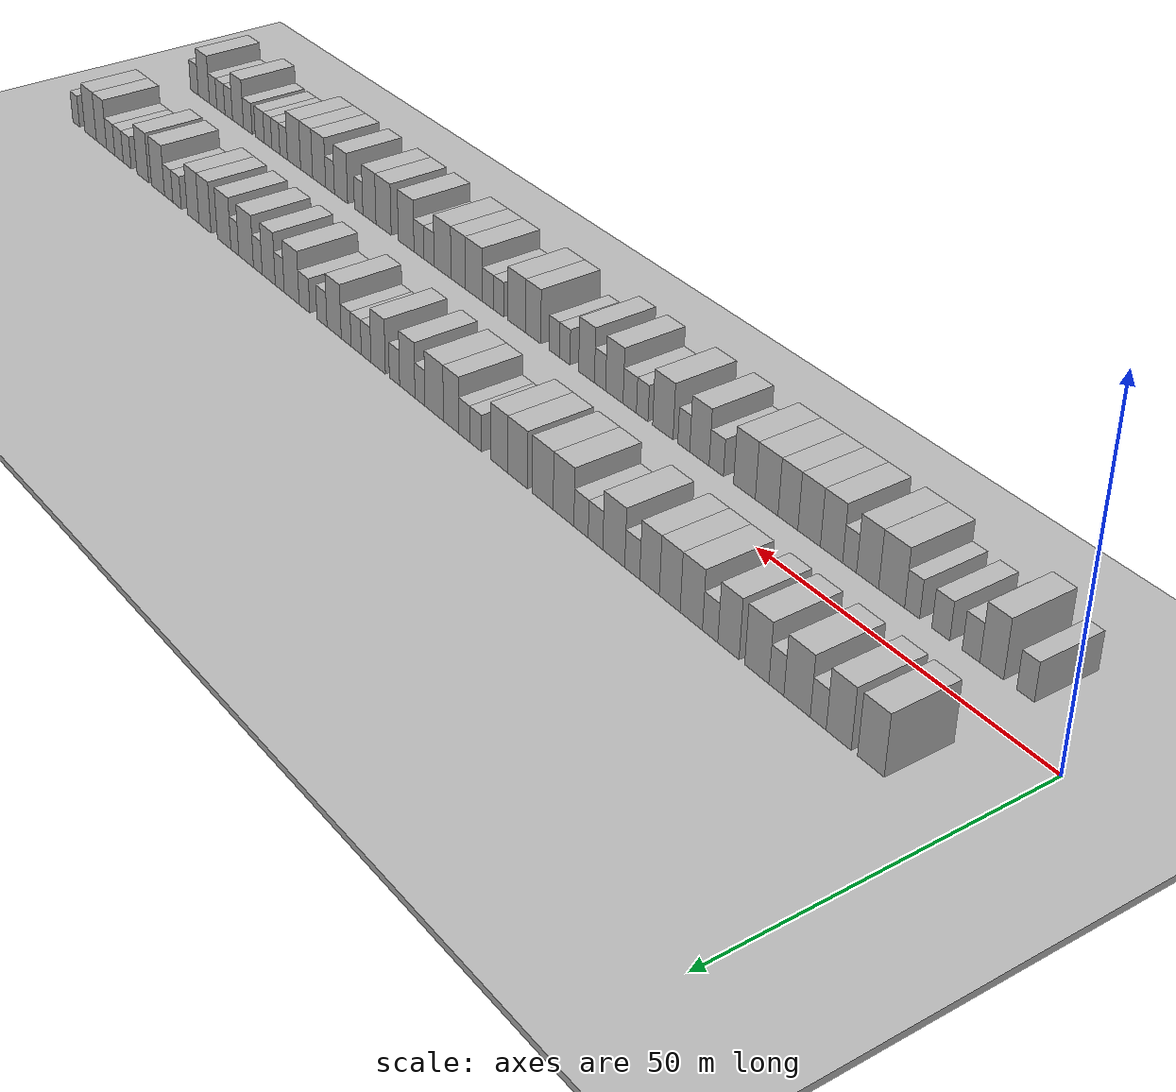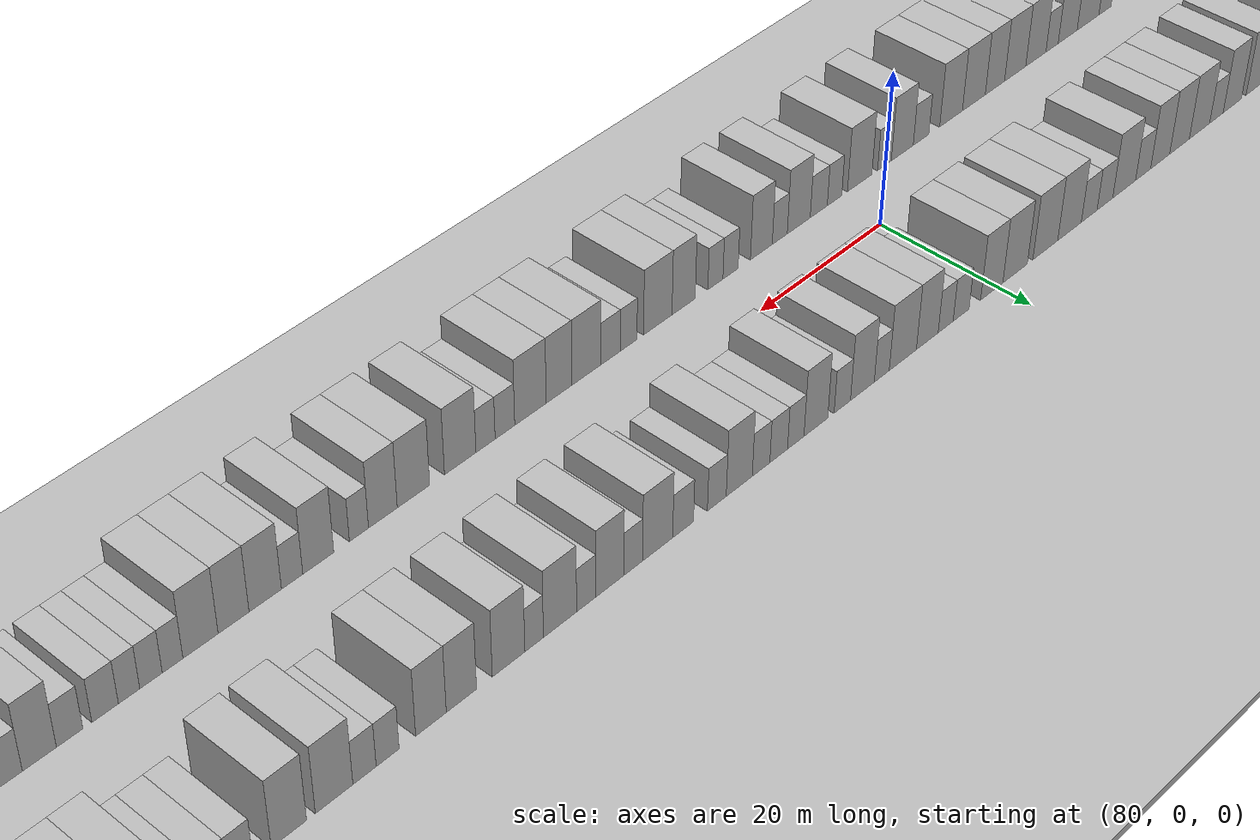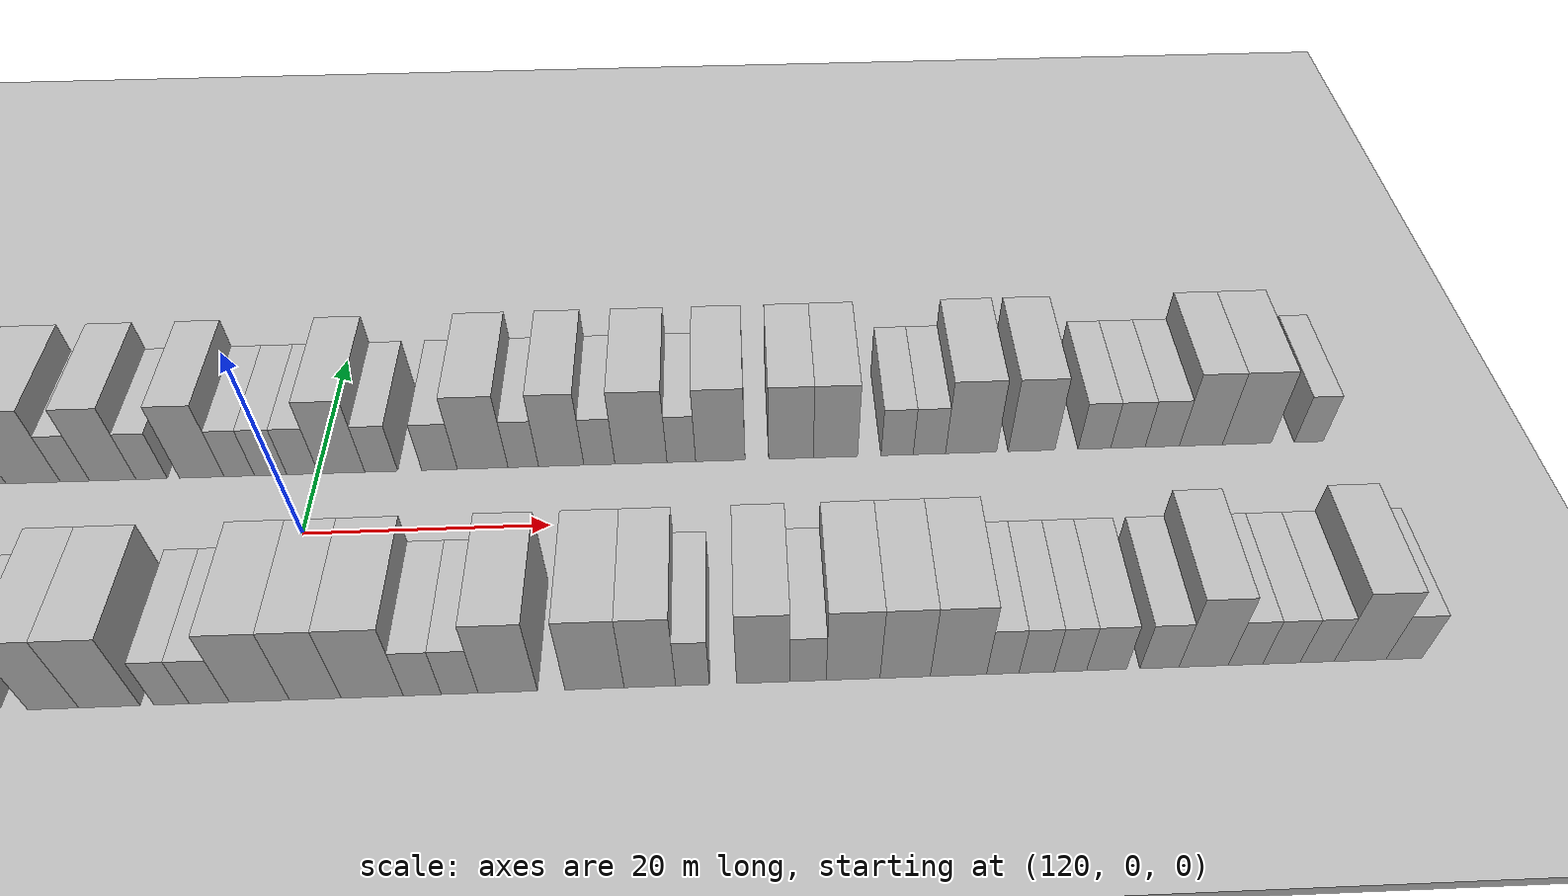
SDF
<?xml version="1.0" encoding="utf-8"?>

<sdf version="1.6">

   <world name="default">

      <gui fullscreen="0">

         <camera name="user_camera">

            <pose>-15 0 4.57585 0 0 0</pose>

            <view_controller>orbit</view_controller>

         </camera>

      </gui>

      <scene>

         <sky>

           <clouds>

             <speed>12</speed>

           </clouds>

         </sky>

         <ambient>0.4 0.4 0.4 1</ambient>

         <background>0.7 0.7 0.7 1</background>

         <shadows>1</shadows>

      </scene>

      <gravity>0 0 -9.8066</gravity>

      <magnetic_field>6e-06 2.3e-05 -4.2e-05</magnetic_field>

      <physics default="0" name="default_physics" type="ode">

         <ode>

            <solver>

               <type>quick</type>

               <iters>10</iters>

               <sor>1.0</sor>

               <use_dynamic_moi_rescaling>0</use_dynamic_moi_rescaling>

            </solver>

            <constraints>

               <cfm>0</cfm>

               <erp>0.2</erp>

               <contact_max_correcting_vel>100</contact_max_correcting_vel>

               <contact_surface_layer>0.001</contact_surface_layer>

            </constraints>

         </ode>

         <max_step_size>0.004</max_step_size>

         <real_time_factor>1</real_time_factor>

         <real_time_update_rate>250</real_time_update_rate>

      </physics>

      <light name="sun" type="directional">

         <cast_shadows>1</cast_shadows>

         <pose>0 0 10 0 0 0</pose>

         <diffuse>0.8 0.8 0.8 1</diffuse>

         <specular>0.2 0.2 0.2 1</specular>

         <attenuation>

            <range>1000</range>

            <constant>0.9</constant>

            <linear>0.01</linear>

            <quadratic>0.001</quadratic>

         </attenuation>

         <direction>-0.5 0.1 -0.9</direction>

      </light>

      <include>

         <name>ground_plane_1</name>

         <uri>model://HANNAS_ground_plane</uri>

         <pose>0 0 0  0 0 0</pose>

      </include>

      <include>

         <name>ground_plane_2</name>

         <uri>model://HANNAS_ground_plane</uri>

         <pose>100 0 0  0 0 0</pose>

      </include>

      <model name="building_1">

         <static>1</static>

         <pose frame="">12.0894 11.0000 0 0.000000 0.000000 1.570796</pose>

         <link name="link">

            <pose frame="">0 0 4.50 0 0 0</pose>

            <collision name="collision">

               <geometry>

                  <box>

                     <size>10.0000 4.1788 9.0000</size>

                  </box>

               </geometry>

               <max_contacts>10</max_contacts>

               <surface>

                  <contact>

                     <ode/>

                  </contact>

                  <bounce/>

                  <friction>

                     <torsional>

                        <ode/>

                     </torsional>

                     <ode/>

                  </friction>

               </surface>

            </collision>

            <visual name="visual">

               <cast_shadows>0</cast_shadows>

               <geometry>

                  <box>

                     <size>10.0000 4.1788 9.0000</size>

                  </box>

               </geometry>

               <material>

                  <script>

                     <uri>model://HANNAS_wall/materials/scripts</uri>

                     <uri>model://HANNAS_wall/materials/textures</uri>

                     <name>vrc/HANNAS_wall</name>

                  </script>

               </material>

            </visual>

            <self_collide>0</self_collide>

            <enable_wind>0</enable_wind>

            <kinematic>0</kinematic>

         </link>

      </model>

      <model name="building_2">

         <static>1</static>

         <pose frame="">17.1828 11.0000 0 0.000000 0.000000 1.570796</pose>

         <link name="link">

            <pose frame="">0 0 4.50 0 0 0</pose>

            <collision name="collision">

               <geometry>

                  <box>

                     <size>10.0000 4.0079 9.0000</size>

                  </box>

               </geometry>

               <max_contacts>10</max_contacts>

               <surface>

                  <contact>

                     <ode/>

                  </contact>

                  <bounce/>

                  <friction>

                     <torsional>

                        <ode/>

                     </torsional>

                     <ode/>

                  </friction>

               </surface>

            </collision>

            <visual name="visual">

               <cast_shadows>0</cast_shadows>

               <geometry>

                  <box>

                     <size>10.0000 4.0079 9.0000</size>

                  </box>

               </geometry>

               <material>

                  <script>

                     <uri>model://HANNAS_wall/materials/scripts</uri>

                     <uri>model://HANNAS_wall/materials/textures</uri>

                     <name>vrc/HANNAS_wall</name>

                  </script>

               </material>

            </visual>

            <self_collide>0</self_collide>

            <enable_wind>0</enable_wind>

            <kinematic>0</kinematic>

         </link>

      </model>

      <model name="building_3">

         <static>1</static>

         <pose frame="">20.4852 11.0000 0 0.000000 0.000000 1.570796</pose>

         <link name="link">

            <pose frame="">0 0 3.00 0 0 0</pose>

            <collision name="collision">

               <geometry>

                  <box>

                     <size>10.0000 2.5969 6.0000</size>

                  </box>

               </geometry>

               <max_contacts>10</max_contacts>

               <surface>

                  <contact>

                     <ode/>

                  </contact>

                  <bounce/>

                  <friction>

                     <torsional>

                        <ode/>

                     </torsional>

                     <ode/>

                  </friction>

               </surface>

            </collision>

            <visual name="visual">

               <cast_shadows>0</cast_shadows>

               <geometry>

                  <box>

                     <size>10.0000 2.5969 6.0000</size>

                  </box>

               </geometry>

               <material>

                  <script>

                     <uri>model://HANNAS_wall/materials/scripts</uri>

                     <uri>model://HANNAS_wall/materials/textures</uri>

                     <name>vrc/HANNAS_wall</name>

                  </script>

               </material>

            </visual>

            <self_collide>0</self_collide>

            <enable_wind>0</enable_wind>

            <kinematic>0</kinematic>

         </link>

      </model>

      <model name="building_4">

         <static>1</static>

         <pose frame="">23.9830 11.0000 0 0.000000 0.000000 1.570796</pose>

         <link name="link">

            <pose frame="">0 0 4.50 0 0 0</pose>

            <collision name="collision">

               <geometry>

                  <box>

                     <size>10.0000 4.3987 9.0000</size>

                  </box>

               </geometry>

               <max_contacts>10</max_contacts>

               <surface>

                  <contact>

                     <ode/>

                  </contact>

                  <bounce/>

                  <friction>

                     <torsional>

                        <ode/>

                     </torsional>

                     <ode/>

                  </friction>

               </surface>

            </collision>

            <visual name="visual">

               <cast_shadows>0</cast_shadows>

               <geometry>

                  <box>

                     <size>10.0000 4.3987 9.0000</size>

                  </box>

               </geometry>

               <material>

                  <script>

                     <uri>model://HANNAS_wall/materials/scripts</uri>

                     <uri>model://HANNAS_wall/materials/textures</uri>

                     <name>vrc/HANNAS_wall</name>

                  </script>

               </material>

            </visual>

            <self_collide>0</self_collide>

            <enable_wind>0</enable_wind>

            <kinematic>0</kinematic>

         </link>

      </model>

      <model name="building_5">

         <static>1</static>

         <pose frame="">27.4589 11.0000 0 0.000000 0.000000 1.570796</pose>

         <link name="link">

            <pose frame="">0 0 3.00 0 0 0</pose>

            <collision name="collision">

               <geometry>

                  <box>

                     <size>10.0000 2.5531 6.0000</size>

                  </box>

               </geometry>

               <max_contacts>10</max_contacts>

               <surface>

                  <contact>

                     <ode/>

                  </contact>

                  <bounce/>

                  <friction>

                     <torsional>

                        <ode/>

                     </torsional>

                     <ode/>

                  </friction>

               </surface>

            </collision>

            <visual name="visual">

               <cast_shadows>0</cast_shadows>

               <geometry>

                  <box>

                     <size>10.0000 2.5531 6.0000</size>

                  </box>

               </geometry>

               <material>

                  <script>

                     <uri>model://HANNAS_wall/materials/scripts</uri>

                     <uri>model://HANNAS_wall/materials/textures</uri>

                     <name>vrc/HANNAS_wall</name>

                  </script>

               </material>

            </visual>

            <self_collide>0</self_collide>

            <enable_wind>0</enable_wind>

            <kinematic>0</kinematic>

         </link>

      </model>

      <model name="building_6">

         <static>1</static>

         <pose frame="">30.8205 11.0000 0 0.000000 0.000000 1.570796</pose>

         <link name="link">

            <pose frame="">0 0 4.50 0 0 0</pose>

            <collision name="collision">

               <geometry>

                  <box>

                     <size>10.0000 4.1700 9.0000</size>

                  </box>

               </geometry>

               <max_contacts>10</max_contacts>

               <surface>

                  <contact>

                     <ode/>

                  </contact>

                  <bounce/>

                  <friction>

                     <torsional>

                        <ode/>

                     </torsional>

                     <ode/>

                  </friction>

               </surface>

            </collision>

            <visual name="visual">

               <cast_shadows>0</cast_shadows>

               <geometry>

                  <box>

                     <size>10.0000 4.1700 9.0000</size>

                  </box>

               </geometry>

               <material>

                  <script>

                     <uri>model://HANNAS_wall/materials/scripts</uri>

                     <uri>model://HANNAS_wall/materials/textures</uri>

                     <name>vrc/HANNAS_wall</name>

                  </script>

               </material>

            </visual>

            <self_collide>0</self_collide>

            <enable_wind>0</enable_wind>

            <kinematic>0</kinematic>

         </link>

      </model>

      <model name="building_7">

         <static>1</static>

         <pose frame="">35.7964 11.0000 0 0.000000 0.000000 1.570796</pose>

         <link name="link">

            <pose frame="">0 0 4.50 0 0 0</pose>

            <collision name="collision">

               <geometry>

                  <box>

                     <size>10.0000 3.7817 9.0000</size>

                  </box>

               </geometry>

               <max_contacts>10</max_contacts>

               <surface>

                  <contact>

                     <ode/>

                  </contact>

                  <bounce/>

                  <friction>

                     <torsional>

                        <ode/>

                     </torsional>

                     <ode/>

                  </friction>

               </surface>

            </collision>

            <visual name="visual">

               <cast_shadows>0</cast_shadows>

               <geometry>

                  <box>

                     <size>10.0000 3.7817 9.0000</size>

                  </box>

               </geometry>

               <material>

                  <script>

                     <uri>model://HANNAS_wall/materials/scripts</uri>

                     <uri>model://HANNAS_wall/materials/textures</uri>

                     <name>vrc/HANNAS_wall</name>

                  </script>

               </material>

            </visual>

            <self_collide>0</self_collide>

            <enable_wind>0</enable_wind>

            <kinematic>0</kinematic>

         </link>

      </model>

      <model name="building_8">

         <static>1</static>

         <pose frame="">39.0722 11.0000 0 0.000000 0.000000 1.570796</pose>

         <link name="link">

            <pose frame="">0 0 3.00 0 0 0</pose>

            <collision name="collision">

               <geometry>

                  <box>

                     <size>10.0000 2.7698 6.0000</size>

                  </box>

               </geometry>

               <max_contacts>10</max_contacts>

               <surface>

                  <contact>

                     <ode/>

                  </contact>

                  <bounce/>

                  <friction>

                     <torsional>

                        <ode/>

                     </torsional>

                     <ode/>

                  </friction>

               </surface>

            </collision>

            <visual name="visual">

               <cast_shadows>0</cast_shadows>

               <geometry>

                  <box>

                     <size>10.0000 2.7698 6.0000</size>

                  </box>

               </geometry>

               <material>

                  <script>

                     <uri>model://HANNAS_wall/materials/scripts</uri>

                     <uri>model://HANNAS_wall/materials/textures</uri>

                     <name>vrc/HANNAS_wall</name>

                  </script>

               </material>

            </visual>

            <self_collide>0</self_collide>

            <enable_wind>0</enable_wind>

            <kinematic>0</kinematic>

         </link>

      </model>

      <model name="building_9">

         <static>1</static>

         <pose frame="">42.5148 11.0000 0 0.000000 0.000000 1.570796</pose>

         <link name="link">

            <pose frame="">0 0 4.50 0 0 0</pose>

            <collision name="collision">

               <geometry>

                  <box>

                     <size>10.0000 4.1155 9.0000</size>

                  </box>

               </geometry>

               <max_contacts>10</max_contacts>

               <surface>

                  <contact>

                     <ode/>

                  </contact>

                  <bounce/>

                  <friction>

                     <torsional>

                        <ode/>

                     </torsional>

                     <ode/>

                  </friction>

               </surface>

            </collision>

            <visual name="visual">

               <cast_shadows>0</cast_shadows>

               <geometry>

                  <box>

                     <size>10.0000 4.1155 9.0000</size>

                  </box>

               </geometry>

               <material>

                  <script>

                     <uri>model://HANNAS_wall/materials/scripts</uri>

                     <uri>model://HANNAS_wall/materials/textures</uri>

                     <name>vrc/HANNAS_wall</name>

                  </script>

               </material>

            </visual>

            <self_collide>0</self_collide>

            <enable_wind>0</enable_wind>

            <kinematic>0</kinematic>

         </link>

      </model>

      <model name="building_10">

         <static>1</static>

         <pose frame="">46.5378 11.0000 0 0.000000 0.000000 1.570796</pose>

         <link name="link">

            <pose frame="">0 0 4.50 0 0 0</pose>

            <collision name="collision">

               <geometry>

                  <box>

                     <size>10.0000 3.9304 9.0000</size>

                  </box>

               </geometry>

               <max_contacts>10</max_contacts>

               <surface>

                  <contact>

                     <ode/>

                  </contact>

                  <bounce/>

                  <friction>

                     <torsional>

                        <ode/>

                     </torsional>

                     <ode/>

                  </friction>

               </surface>

            </collision>

            <visual name="visual">

               <cast_shadows>0</cast_shadows>

               <geometry>

                  <box>

                     <size>10.0000 3.9304 9.0000</size>

                  </box>

               </geometry>

               <material>

                  <script>

                     <uri>model://HANNAS_wall/materials/scripts</uri>

                     <uri>model://HANNAS_wall/materials/textures</uri>

                     <name>vrc/HANNAS_wall</name>

                  </script>

               </material>

            </visual>

            <self_collide>0</self_collide>

            <enable_wind>0</enable_wind>

            <kinematic>0</kinematic>

         </link>

      </model>

      <model name="building_11">

         <static>1</static>

         <pose frame="">50.3822 11.0000 0 0.000000 0.000000 1.570796</pose>

         <link name="link">

            <pose frame="">0 0 4.50 0 0 0</pose>

            <collision name="collision">

               <geometry>

                  <box>

                     <size>10.0000 3.7583 9.0000</size>

                  </box>

               </geometry>

               <max_contacts>10</max_contacts>

               <surface>

                  <contact>

                     <ode/>

                  </contact>

                  <bounce/>

                  <friction>

                     <torsional>

                        <ode/>

                     </torsional>

                     <ode/>

                  </friction>

               </surface>

            </collision>

            <visual name="visual">

               <cast_shadows>0</cast_shadows>

               <geometry>

                  <box>

                     <size>10.0000 3.7583 9.0000</size>

                  </box>

               </geometry>

               <material>

                  <script>

                     <uri>model://HANNAS_wall/materials/scripts</uri>

                     <uri>model://HANNAS_wall/materials/textures</uri>

                     <name>vrc/HANNAS_wall</name>

                  </script>

               </material>

            </visual>

            <self_collide>0</self_collide>

            <enable_wind>0</enable_wind>

            <kinematic>0</kinematic>

         </link>

      </model>

      <model name="building_12">

         <static>1</static>

         <pose frame="">53.7239 11.0000 0 0.000000 0.000000 1.570796</pose>

         <link name="link">

            <pose frame="">0 0 3.00 0 0 0</pose>

            <collision name="collision">

               <geometry>

                  <box>

                     <size>10.0000 2.9252 6.0000</size>

                  </box>

               </geometry>

               <max_contacts>10</max_contacts>

               <surface>

                  <contact>

                     <ode/>

                  </contact>

                  <bounce/>

                  <friction>

                     <torsional>

                        <ode/>

                     </torsional>

                     <ode/>

                  </friction>

               </surface>

            </collision>

            <visual name="visual">

               <cast_shadows>0</cast_shadows>

               <geometry>

                  <box>

                     <size>10.0000 2.9252 6.0000</size>

                  </box>

               </geometry>

               <material>

                  <script>

                     <uri>model://HANNAS_wall/materials/scripts</uri>

                     <uri>model://HANNAS_wall/materials/textures</uri>

                     <name>vrc/HANNAS_wall</name>

                  </script>

               </material>

            </visual>

            <self_collide>0</self_collide>

            <enable_wind>0</enable_wind>

            <kinematic>0</kinematic>

         </link>

      </model>

      <model name="building_13">

         <static>1</static>

         <pose frame="">57.3738 11.0000 0 0.000000 0.000000 1.570796</pose>

         <link name="link">

            <pose frame="">0 0 4.50 0 0 0</pose>

            <collision name="collision">

               <geometry>

                  <box>

                     <size>10.0000 4.3746 9.0000</size>

                  </box>

               </geometry>

               <max_contacts>10</max_contacts>

               <surface>

                  <contact>

                     <ode/>

                  </contact>

                  <bounce/>

                  <friction>

                     <torsional>

                        <ode/>

                     </torsional>

                     <ode/>

                  </friction>

               </surface>

            </collision>

            <visual name="visual">

               <cast_shadows>0</cast_shadows>

               <geometry>

                  <box>

                     <size>10.0000 4.3746 9.0000</size>

                  </box>

               </geometry>

               <material>

                  <script>

                     <uri>model://HANNAS_wall/materials/scripts</uri>

                     <uri>model://HANNAS_wall/materials/textures</uri>

                     <name>vrc/HANNAS_wall</name>

                  </script>

               </material>

            </visual>

            <self_collide>0</self_collide>

            <enable_wind>0</enable_wind>

            <kinematic>0</kinematic>

         </link>

      </model>

      <model name="building_14">

         <static>1</static>

         <pose frame="">61.0347 11.0000 0 0.000000 0.000000 1.570796</pose>

         <link name="link">

            <pose frame="">0 0 3.00 0 0 0</pose>

            <collision name="collision">

               <geometry>

                  <box>

                     <size>10.0000 2.9471 6.0000</size>

                  </box>

               </geometry>

               <max_contacts>10</max_contacts>

               <surface>

                  <contact>

                     <ode/>

                  </contact>

                  <bounce/>

                  <friction>

                     <torsional>

                        <ode/>

                     </torsional>

                     <ode/>

                  </friction>

               </surface>

            </collision>

            <visual name="visual">

               <cast_shadows>0</cast_shadows>

               <geometry>

                  <box>

                     <size>10.0000 2.9471 6.0000</size>

                  </box>

               </geometry>

               <material>

                  <script>

                     <uri>model://HANNAS_wall/materials/scripts</uri>

                     <uri>model://HANNAS_wall/materials/textures</uri>

                     <name>vrc/HANNAS_wall</name>

                  </script>

               </material>

            </visual>

            <self_collide>0</self_collide>

            <enable_wind>0</enable_wind>

            <kinematic>0</kinematic>

         </link>

      </model>

      <model name="building_15">

         <static>1</static>

         <pose frame="">63.9837 11.0000 0 0.000000 0.000000 1.570796</pose>

         <link name="link">

            <pose frame="">0 0 3.00 0 0 0</pose>

            <collision name="collision">

               <geometry>

                  <box>

                     <size>10.0000 2.9508 6.0000</size>

                  </box>

               </geometry>

               <max_contacts>10</max_contacts>

               <surface>

                  <contact>

                     <ode/>

                  </contact>

                  <bounce/>

                  <friction>

                     <torsional>

                        <ode/>

                     </torsional>

                     <ode/>

                  </friction>

               </surface>

            </collision>

            <visual name="visual">

               <cast_shadows>0</cast_shadows>

               <geometry>

                  <box>

                     <size>10.0000 2.9508 6.0000</size>

                  </box>

               </geometry>

               <material>

                  <script>

                     <uri>model://HANNAS_wall/materials/scripts</uri>

                     <uri>model://HANNAS_wall/materials/textures</uri>

                     <name>vrc/HANNAS_wall</name>

                  </script>

               </material>

            </visual>

            <self_collide>0</self_collide>

            <enable_wind>0</enable_wind>

            <kinematic>0</kinematic>

         </link>

      </model>

      <model name="building_16">

         <static>1</static>

         <pose frame="">67.6366 11.0000 0 0.000000 0.000000 1.570796</pose>

         <link name="link">

            <pose frame="">0 0 4.50 0 0 0</pose>

            <collision name="collision">

               <geometry>

                  <box>

                     <size>10.0000 4.3550 9.0000</size>

                  </box>

               </geometry>

               <max_contacts>10</max_contacts>

               <surface>

                  <contact>

                     <ode/>

                  </contact>

                  <bounce/>

                  <friction>

                     <torsional>

                        <ode/>

                     </torsional>

                     <ode/>

                  </friction>

               </surface>

            </collision>

            <visual name="visual">

               <cast_shadows>0</cast_shadows>

               <geometry>

                  <box>

                     <size>10.0000 4.3550 9.0000</size>

                  </box>

               </geometry>

               <material>

                  <script>

                     <uri>model://HANNAS_wall/materials/scripts</uri>

                     <uri>model://HANNAS_wall/materials/textures</uri>

                     <name>vrc/HANNAS_wall</name>

                  </script>

               </material>

            </visual>

            <self_collide>0</self_collide>

            <enable_wind>0</enable_wind>

            <kinematic>0</kinematic>

         </link>

      </model>

      <model name="building_17">

         <static>1</static>

         <pose frame="">72.0608 11.0000 0 0.000000 0.000000 1.570796</pose>

         <link name="link">

            <pose frame="">0 0 4.50 0 0 0</pose>

            <collision name="collision">

               <geometry>

                  <box>

                     <size>10.0000 4.4936 9.0000</size>

                  </box>

               </geometry>

               <max_contacts>10</max_contacts>

               <surface>

                  <contact>

                     <ode/>

                  </contact>

                  <bounce/>

                  <friction>

                     <torsional>

                        <ode/>

                     </torsional>

                     <ode/>

                  </friction>

               </surface>

            </collision>

            <visual name="visual">

               <cast_shadows>0</cast_shadows>

               <geometry>

                  <box>

                     <size>10.0000 4.4936 9.0000</size>

                  </box>

               </geometry>

               <material>

                  <script>

                     <uri>model://HANNAS_wall/materials/scripts</uri>

                     <uri>model://HANNAS_wall/materials/textures</uri>

                     <name>vrc/HANNAS_wall</name>

                  </script>

               </material>

            </visual>

            <self_collide>0</self_collide>

            <enable_wind>0</enable_wind>

            <kinematic>0</kinematic>

         </link>

      </model>

      <model name="building_18">

         <static>1</static>

         <pose frame="">77.4810 11.0000 0 0.000000 0.000000 1.570796</pose>

         <link name="link">

            <pose frame="">0 0 4.50 0 0 0</pose>

            <collision name="collision">

               <geometry>

                  <box>

                     <size>10.0000 4.3468 9.0000</size>

                  </box>

               </geometry>

               <max_contacts>10</max_contacts>

               <surface>

                  <contact>

                     <ode/>

                  </contact>

                  <bounce/>

                  <friction>

                     <torsional>

                        <ode/>

                     </torsional>

                     <ode/>

                  </friction>

               </surface>

            </collision>

            <visual name="visual">

               <cast_shadows>0</cast_shadows>

               <geometry>

                  <box>

                     <size>10.0000 4.3468 9.0000</size>

                  </box>

               </geometry>

               <material>

                  <script>

                     <uri>model://HANNAS_wall/materials/scripts</uri>

                     <uri>model://HANNAS_wall/materials/textures</uri>

                     <name>vrc/HANNAS_wall</name>

                  </script>

               </material>

            </visual>

            <self_collide>0</self_collide>

            <enable_wind>0</enable_wind>

            <kinematic>0</kinematic>

         </link>

      </model>

      <model name="building_19">

         <static>1</static>

         <pose frame="">81.5940 11.0000 0 0.000000 0.000000 1.570796</pose>

         <link name="link">

            <pose frame="">0 0 4.50 0 0 0</pose>

            <collision name="collision">

               <geometry>

                  <box>

                     <size>10.0000 3.8792 9.0000</size>

                  </box>

               </geometry>

               <max_contacts>10</max_contacts>

               <surface>

                  <contact>

                     <ode/>

                  </contact>

                  <bounce/>

                  <friction>

                     <torsional>

                        <ode/>

                     </torsional>

                     <ode/>

                  </friction>

               </surface>

            </collision>

            <visual name="visual">

               <cast_shadows>0</cast_shadows>

               <geometry>

                  <box>

                     <size>10.0000 3.8792 9.0000</size>

                  </box>

               </geometry>

               <material>

                  <script>

                     <uri>model://HANNAS_wall/materials/scripts</uri>

                     <uri>model://HANNAS_wall/materials/textures</uri>

                     <name>vrc/HANNAS_wall</name>

                  </script>

               </material>

            </visual>

            <self_collide>0</self_collide>

            <enable_wind>0</enable_wind>

            <kinematic>0</kinematic>

         </link>

      </model>

      <model name="building_20">

         <static>1</static>

         <pose frame="">86.8981 11.0000 0 0.000000 0.000000 1.570796</pose>

         <link name="link">

            <pose frame="">0 0 3.00 0 0 0</pose>

            <collision name="collision">

               <geometry>

                  <box>

                     <size>10.0000 2.7290 6.0000</size>

                  </box>

               </geometry>

               <max_contacts>10</max_contacts>

               <surface>

                  <contact>

                     <ode/>

                  </contact>

                  <bounce/>

                  <friction>

                     <torsional>

                        <ode/>

                     </torsional>

                     <ode/>

                  </friction>

               </surface>

            </collision>

            <visual name="visual">

               <cast_shadows>0</cast_shadows>

               <geometry>

                  <box>

                     <size>10.0000 2.7290 6.0000</size>

                  </box>

               </geometry>

               <material>

                  <script>

                     <uri>model://HANNAS_wall/materials/scripts</uri>

                     <uri>model://HANNAS_wall/materials/textures</uri>

                     <name>vrc/HANNAS_wall</name>

                  </script>

               </material>

            </visual>

            <self_collide>0</self_collide>

            <enable_wind>0</enable_wind>

            <kinematic>0</kinematic>

         </link>

      </model>

      <model name="building_21">

         <static>1</static>

         <pose frame="">89.5289 11.0000 0 0.000000 0.000000 1.570796</pose>

         <link name="link">

            <pose frame="">0 0 3.00 0 0 0</pose>

            <collision name="collision">

               <geometry>

                  <box>

                     <size>10.0000 2.5326 6.0000</size>

                  </box>

               </geometry>

               <max_contacts>10</max_contacts>

               <surface>

                  <contact>

                     <ode/>

                  </contact>

                  <bounce/>

                  <friction>

                     <torsional>

                        <ode/>

                     </torsional>

                     <ode/>

                  </friction>

               </surface>

            </collision>

            <visual name="visual">

               <cast_shadows>0</cast_shadows>

               <geometry>

                  <box>

                     <size>10.0000 2.5326 6.0000</size>

                  </box>

               </geometry>

               <material>

                  <script>

                     <uri>model://HANNAS_wall/materials/scripts</uri>

                     <uri>model://HANNAS_wall/materials/textures</uri>

                     <name>vrc/HANNAS_wall</name>

                  </script>

               </material>

            </visual>

            <self_collide>0</self_collide>

            <enable_wind>0</enable_wind>

            <kinematic>0</kinematic>

         </link>

      </model>

      <model name="building_22">

         <static>1</static>

         <pose frame="">92.6127 11.0000 0 0.000000 0.000000 1.570796</pose>

         <link name="link">

            <pose frame="">0 0 4.50 0 0 0</pose>

            <collision name="collision">

               <geometry>

                  <box>

                     <size>10.0000 3.6350 9.0000</size>

                  </box>

               </geometry>

               <max_contacts>10</max_contacts>

               <surface>

                  <contact>

                     <ode/>

                  </contact>

                  <bounce/>

                  <friction>

                     <torsional>

                        <ode/>

                     </torsional>

                     <ode/>

                  </friction>

               </surface>

            </collision>

            <visual name="visual">

               <cast_shadows>0</cast_shadows>

               <geometry>

                  <box>

                     <size>10.0000 3.6350 9.0000</size>

                  </box>

               </geometry>

               <material>

                  <script>

                     <uri>model://HANNAS_wall/materials/scripts</uri>

                     <uri>model://HANNAS_wall/materials/textures</uri>

                     <name>vrc/HANNAS_wall</name>

                  </script>

               </material>

            </visual>

            <self_collide>0</self_collide>

            <enable_wind>0</enable_wind>

            <kinematic>0</kinematic>

         </link>

      </model>

      <model name="building_23">

         <static>1</static>

         <pose frame="">96.6629 11.0000 0 0.000000 0.000000 1.570796</pose>

         <link name="link">

            <pose frame="">0 0 4.50 0 0 0</pose>

            <collision name="collision">

               <geometry>

                  <box>

                     <size>10.0000 4.4656 9.0000</size>

                  </box>

               </geometry>

               <max_contacts>10</max_contacts>

               <surface>

                  <contact>

                     <ode/>

                  </contact>

                  <bounce/>

                  <friction>

                     <torsional>

                        <ode/>

                     </torsional>

                     <ode/>

                  </friction>

               </surface>

            </collision>

            <visual name="visual">

               <cast_shadows>0</cast_shadows>

               <geometry>

                  <box>

                     <size>10.0000 4.4656 9.0000</size>

                  </box>

               </geometry>

               <material>

                  <script>

                     <uri>model://HANNAS_wall/materials/scripts</uri>

                     <uri>model://HANNAS_wall/materials/textures</uri>

                     <name>vrc/HANNAS_wall</name>

                  </script>

               </material>

            </visual>

            <self_collide>0</self_collide>

            <enable_wind>0</enable_wind>

            <kinematic>0</kinematic>

         </link>

      </model>

      <model name="building_24">

         <static>1</static>

         <pose frame="">100.1075 11.0000 0 0.000000 0.000000 1.570796</pose>

         <link name="link">

            <pose frame="">0 0 3.00 0 0 0</pose>

            <collision name="collision">

               <geometry>

                  <box>

                     <size>10.0000 2.4235 6.0000</size>

                  </box>

               </geometry>

               <max_contacts>10</max_contacts>

               <surface>

                  <contact>

                     <ode/>

                  </contact>

                  <bounce/>

                  <friction>

                     <torsional>

                        <ode/>

                     </torsional>

                     <ode/>

                  </friction>

               </surface>

            </collision>

            <visual name="visual">

               <cast_shadows>0</cast_shadows>

               <geometry>

                  <box>

                     <size>10.0000 2.4235 6.0000</size>

                  </box>

               </geometry>

               <material>

                  <script>

                     <uri>model://HANNAS_wall/materials/scripts</uri>

                     <uri>model://HANNAS_wall/materials/textures</uri>

                     <name>vrc/HANNAS_wall</name>

                  </script>

               </material>

            </visual>

            <self_collide>0</self_collide>

            <enable_wind>0</enable_wind>

            <kinematic>0</kinematic>

         </link>

      </model>

      <model name="building_25">

         <static>1</static>

         <pose frame="">103.2230 11.0000 0 0.000000 0.000000 1.570796</pose>

         <link name="link">

            <pose frame="">0 0 4.50 0 0 0</pose>

            <collision name="collision">

               <geometry>

                  <box>

                     <size>10.0000 3.8074 9.0000</size>

                  </box>

               </geometry>

               <max_contacts>10</max_contacts>

               <surface>

                  <contact>

                     <ode/>

                  </contact>

                  <bounce/>

                  <friction>

                     <torsional>

                        <ode/>

                     </torsional>

                     <ode/>

                  </friction>

               </surface>

            </collision>

            <visual name="visual">

               <cast_shadows>0</cast_shadows>

               <geometry>

                  <box>

                     <size>10.0000 3.8074 9.0000</size>

                  </box>

               </geometry>

               <material>

                  <script>

                     <uri>model://HANNAS_wall/materials/scripts</uri>

                     <uri>model://HANNAS_wall/materials/textures</uri>

                     <name>vrc/HANNAS_wall</name>

                  </script>

               </material>

            </visual>

            <self_collide>0</self_collide>

            <enable_wind>0</enable_wind>

            <kinematic>0</kinematic>

         </link>

      </model>

      <model name="building_26">

         <static>1</static>

         <pose frame="">106.4189 11.0000 0 0.000000 0.000000 1.570796</pose>

         <link name="link">

            <pose frame="">0 0 3.00 0 0 0</pose>

            <collision name="collision">

               <geometry>

                  <box>

                     <size>10.0000 2.5844 6.0000</size>

                  </box>

               </geometry>

               <max_contacts>10</max_contacts>

               <surface>

                  <contact>

                     <ode/>

                  </contact>

                  <bounce/>

                  <friction>

                     <torsional>

                        <ode/>

                     </torsional>

                     <ode/>

                  </friction>

               </surface>

            </collision>

            <visual name="visual">

               <cast_shadows>0</cast_shadows>

               <geometry>

                  <box>

                     <size>10.0000 2.5844 6.0000</size>

                  </box>

               </geometry>

               <material>

                  <script>

                     <uri>model://HANNAS_wall/materials/scripts</uri>

                     <uri>model://HANNAS_wall/materials/textures</uri>

                     <name>vrc/HANNAS_wall</name>

                  </script>

               </material>

            </visual>

            <self_collide>0</self_collide>

            <enable_wind>0</enable_wind>

            <kinematic>0</kinematic>

         </link>

      </model>

      <model name="building_27">

         <static>1</static>

         <pose frame="">110.5554 11.0000 0 0.000000 0.000000 1.570796</pose>

         <link name="link">

            <pose frame="">0 0 4.50 0 0 0</pose>

            <collision name="collision">

               <geometry>

                  <box>

                     <size>10.0000 3.6886 9.0000</size>

                  </box>

               </geometry>

               <max_contacts>10</max_contacts>

               <surface>

                  <contact>

                     <ode/>

                  </contact>

                  <bounce/>

                  <friction>

                     <torsional>

                        <ode/>

                     </torsional>

                     <ode/>

                  </friction>

               </surface>

            </collision>

            <visual name="visual">

               <cast_shadows>0</cast_shadows>

               <geometry>

                  <box>

                     <size>10.0000 3.6886 9.0000</size>

                  </box>

               </geometry>

               <material>

                  <script>

                     <uri>model://HANNAS_wall/materials/scripts</uri>

                     <uri>model://HANNAS_wall/materials/textures</uri>

                     <name>vrc/HANNAS_wall</name>

                  </script>

               </material>

            </visual>

            <self_collide>0</self_collide>

            <enable_wind>0</enable_wind>

            <kinematic>0</kinematic>

         </link>

      </model>

      <model name="building_28">

         <static>1</static>

         <pose frame="">113.6621 11.0000 0 0.000000 0.000000 1.570796</pose>

         <link name="link">

            <pose frame="">0 0 3.00 0 0 0</pose>

            <collision name="collision">

               <geometry>

                  <box>

                     <size>10.0000 2.5249 6.0000</size>

                  </box>

               </geometry>

               <max_contacts>10</max_contacts>

               <surface>

                  <contact>

                     <ode/>

                  </contact>

                  <bounce/>

                  <friction>

                     <torsional>

                        <ode/>

                     </torsional>

                     <ode/>

                  </friction>

               </surface>

            </collision>

            <visual name="visual">

               <cast_shadows>0</cast_shadows>

               <geometry>

                  <box>

                     <size>10.0000 2.5249 6.0000</size>

                  </box>

               </geometry>

               <material>

                  <script>

                     <uri>model://HANNAS_wall/materials/scripts</uri>

                     <uri>model://HANNAS_wall/materials/textures</uri>

                     <name>vrc/HANNAS_wall</name>

                  </script>

               </material>

            </visual>

            <self_collide>0</self_collide>

            <enable_wind>0</enable_wind>

            <kinematic>0</kinematic>

         </link>

      </model>

      <model name="building_29">

         <static>1</static>

         <pose frame="">116.2652 11.0000 0 0.000000 0.000000 1.570796</pose>

         <link name="link">

            <pose frame="">0 0 3.00 0 0 0</pose>

            <collision name="collision">

               <geometry>

                  <box>

                     <size>10.0000 2.6814 6.0000</size>

                  </box>

               </geometry>

               <max_contacts>10</max_contacts>

               <surface>

                  <contact>

                     <ode/>

                  </contact>

                  <bounce/>

                  <friction>

                     <torsional>

                        <ode/>

                     </torsional>

                     <ode/>

                  </friction>

               </surface>

            </collision>

            <visual name="visual">

               <cast_shadows>0</cast_shadows>

               <geometry>

                  <box>

                     <size>10.0000 2.6814 6.0000</size>

                  </box>

               </geometry>

               <material>

                  <script>

                     <uri>model://HANNAS_wall/materials/scripts</uri>

                     <uri>model://HANNAS_wall/materials/textures</uri>

                     <name>vrc/HANNAS_wall</name>

                  </script>

               </material>

            </visual>

            <self_collide>0</self_collide>

            <enable_wind>0</enable_wind>

            <kinematic>0</kinematic>

         </link>

      </model>

      <model name="building_30">

         <static>1</static>

         <pose frame="">118.9211 11.0000 0 0.000000 0.000000 1.570796</pose>

         <link name="link">

            <pose frame="">0 0 3.00 0 0 0</pose>

            <collision name="collision">

               <geometry>

                  <box>

                     <size>10.0000 2.6303 6.0000</size>

                  </box>

               </geometry>

               <max_contacts>10</max_contacts>

               <surface>

                  <contact>

                     <ode/>

                  </contact>

                  <bounce/>

                  <friction>

                     <torsional>

                        <ode/>

                     </torsional>

                     <ode/>

                  </friction>

               </surface>

            </collision>

            <visual name="visual">

               <cast_shadows>0</cast_shadows>

               <geometry>

                  <box>

                     <size>10.0000 2.6303 6.0000</size>

                  </box>

               </geometry>

               <material>

                  <script>

                     <uri>model://HANNAS_wall/materials/scripts</uri>

                     <uri>model://HANNAS_wall/materials/textures</uri>

                     <name>vrc/HANNAS_wall</name>

                  </script>

               </material>

            </visual>

            <self_collide>0</self_collide>

            <enable_wind>0</enable_wind>

            <kinematic>0</kinematic>

         </link>

      </model>

      <model name="building_31">

         <static>1</static>

         <pose frame="">122.1619 11.0000 0 0.000000 0.000000 1.570796</pose>

         <link name="link">

            <pose frame="">0 0 4.50 0 0 0</pose>

            <collision name="collision">

               <geometry>

                  <box>

                     <size>10.0000 3.8514 9.0000</size>

                  </box>

               </geometry>

               <max_contacts>10</max_contacts>

               <surface>

                  <contact>

                     <ode/>

                  </contact>

                  <bounce/>

                  <friction>

                     <torsional>

                        <ode/>

                     </torsional>

                     <ode/>

                  </friction>

               </surface>

            </collision>

            <visual name="visual">

               <cast_shadows>0</cast_shadows>

               <geometry>

                  <box>

                     <size>10.0000 3.8514 9.0000</size>

                  </box>

               </geometry>

               <material>

                  <script>

                     <uri>model://HANNAS_wall/materials/scripts</uri>

                     <uri>model://HANNAS_wall/materials/textures</uri>

                     <name>vrc/HANNAS_wall</name>

                  </script>

               </material>

            </visual>

            <self_collide>0</self_collide>

            <enable_wind>0</enable_wind>

            <kinematic>0</kinematic>

         </link>

      </model>

      <model name="building_32">

         <static>1</static>

         <pose frame="">125.4590 11.0000 0 0.000000 0.000000 1.570796</pose>

         <link name="link">

            <pose frame="">0 0 3.00 0 0 0</pose>

            <collision name="collision">

               <geometry>

                  <box>

                     <size>10.0000 2.7426 6.0000</size>

                  </box>

               </geometry>

               <max_contacts>10</max_contacts>

               <surface>

                  <contact>

                     <ode/>

                  </contact>

                  <bounce/>

                  <friction>

                     <torsional>

                        <ode/>

                     </torsional>

                     <ode/>

                  </friction>

               </surface>

            </collision>

            <visual name="visual">

               <cast_shadows>0</cast_shadows>

               <geometry>

                  <box>

                     <size>10.0000 2.7426 6.0000</size>

                  </box>

               </geometry>

               <material>

                  <script>

                     <uri>model://HANNAS_wall/materials/scripts</uri>

                     <uri>model://HANNAS_wall/materials/textures</uri>

                     <name>vrc/HANNAS_wall</name>

                  </script>

               </material>

            </visual>

            <self_collide>0</self_collide>

            <enable_wind>0</enable_wind>

            <kinematic>0</kinematic>

         </link>

      </model>

      <model name="building_33">

         <static>1</static>

         <pose frame="">130.3194 11.0000 0 0.000000 0.000000 1.570796</pose>

         <link name="link">

            <pose frame="">0 0 3.00 0 0 0</pose>

            <collision name="collision">

               <geometry>

                  <box>

                     <size>10.0000 2.9783 6.0000</size>

                  </box>

               </geometry>

               <max_contacts>10</max_contacts>

               <surface>

                  <contact>

                     <ode/>

                  </contact>

                  <bounce/>

                  <friction>

                     <torsional>

                        <ode/>

                     </torsional>

                     <ode/>

                  </friction>

               </surface>

            </collision>

            <visual name="visual">

               <cast_shadows>0</cast_shadows>

               <geometry>

                  <box>

                     <size>10.0000 2.9783 6.0000</size>

                  </box>

               </geometry>

               <material>

                  <script>

                     <uri>model://HANNAS_wall/materials/scripts</uri>

                     <uri>model://HANNAS_wall/materials/textures</uri>

                     <name>vrc/HANNAS_wall</name>

                  </script>

               </material>

            </visual>

            <self_collide>0</self_collide>

            <enable_wind>0</enable_wind>

            <kinematic>0</kinematic>

         </link>

      </model>

      <model name="building_34">

         <static>1</static>

         <pose frame="">133.9288 11.0000 0 0.000000 0.000000 1.570796</pose>

         <link name="link">

            <pose frame="">0 0 4.50 0 0 0</pose>

            <collision name="collision">

               <geometry>

                  <box>

                     <size>10.0000 4.2404 9.0000</size>

                  </box>

               </geometry>

               <max_contacts>10</max_contacts>

               <surface>

                  <contact>

                     <ode/>

                  </contact>

                  <bounce/>

                  <friction>

                     <torsional>

                        <ode/>

                     </torsional>

                     <ode/>

                  </friction>

               </surface>

            </collision>

            <visual name="visual">

               <cast_shadows>0</cast_shadows>

               <geometry>

                  <box>

                     <size>10.0000 4.2404 9.0000</size>

                  </box>

               </geometry>

               <material>

                  <script>

                     <uri>model://HANNAS_wall/materials/scripts</uri>

                     <uri>model://HANNAS_wall/materials/textures</uri>

                     <name>vrc/HANNAS_wall</name>

                  </script>

               </material>

            </visual>

            <self_collide>0</self_collide>

            <enable_wind>0</enable_wind>

            <kinematic>0</kinematic>

         </link>

      </model>

      <model name="building_35">

         <static>1</static>

         <pose frame="">137.3306 11.0000 0 0.000000 0.000000 1.570796</pose>

         <link name="link">

            <pose frame="">0 0 3.00 0 0 0</pose>

            <collision name="collision">

               <geometry>

                  <box>

                     <size>10.0000 2.5633 6.0000</size>

                  </box>

               </geometry>

               <max_contacts>10</max_contacts>

               <surface>

                  <contact>

                     <ode/>

                  </contact>

                  <bounce/>

                  <friction>

                     <torsional>

                        <ode/>

                     </torsional>

                     <ode/>

                  </friction>

               </surface>

            </collision>

            <visual name="visual">

               <cast_shadows>0</cast_shadows>

               <geometry>

                  <box>

                     <size>10.0000 2.5633 6.0000</size>

                  </box>

               </geometry>

               <material>

                  <script>

                     <uri>model://HANNAS_wall/materials/scripts</uri>

                     <uri>model://HANNAS_wall/materials/textures</uri>

                     <name>vrc/HANNAS_wall</name>

                  </script>

               </material>

            </visual>

            <self_collide>0</self_collide>

            <enable_wind>0</enable_wind>

            <kinematic>0</kinematic>

         </link>

      </model>

      <model name="building_36">

         <static>1</static>

         <pose frame="">140.5159 11.0000 0 0.000000 0.000000 1.570796</pose>

         <link name="link">

            <pose frame="">0 0 4.50 0 0 0</pose>

            <collision name="collision">

               <geometry>

                  <box>

                     <size>10.0000 3.8072 9.0000</size>

                  </box>

               </geometry>

               <max_contacts>10</max_contacts>

               <surface>

                  <contact>

                     <ode/>

                  </contact>

                  <bounce/>

                  <friction>

                     <torsional>

                        <ode/>

                     </torsional>

                     <ode/>

                  </friction>

               </surface>

            </collision>

            <visual name="visual">

               <cast_shadows>0</cast_shadows>

               <geometry>

                  <box>

                     <size>10.0000 3.8072 9.0000</size>

                  </box>

               </geometry>

               <material>

                  <script>

                     <uri>model://HANNAS_wall/materials/scripts</uri>

                     <uri>model://HANNAS_wall/materials/textures</uri>

                     <name>vrc/HANNAS_wall</name>

                  </script>

               </material>

            </visual>

            <self_collide>0</self_collide>

            <enable_wind>0</enable_wind>

            <kinematic>0</kinematic>

         </link>

      </model>

      <model name="building_37">

         <static>1</static>

         <pose frame="">143.7232 11.0000 0 0.000000 0.000000 1.570796</pose>

         <link name="link">

            <pose frame="">0 0 3.00 0 0 0</pose>

            <collision name="collision">

               <geometry>

                  <box>

                     <size>10.0000 2.6073 6.0000</size>

                  </box>

               </geometry>

               <max_contacts>10</max_contacts>

               <surface>

                  <contact>

                     <ode/>

                  </contact>

                  <bounce/>

                  <friction>

                     <torsional>

                        <ode/>

                     </torsional>

                     <ode/>

                  </friction>

               </surface>

            </collision>

            <visual name="visual">

               <cast_shadows>0</cast_shadows>

               <geometry>

                  <box>

                     <size>10.0000 2.6073 6.0000</size>

                  </box>

               </geometry>

               <material>

                  <script>

                     <uri>model://HANNAS_wall/materials/scripts</uri>

                     <uri>model://HANNAS_wall/materials/textures</uri>

                     <name>vrc/HANNAS_wall</name>

                  </script>

               </material>

            </visual>

            <self_collide>0</self_collide>

            <enable_wind>0</enable_wind>

            <kinematic>0</kinematic>

         </link>

      </model>

      <model name="building_38">

         <static>1</static>

         <pose frame="">147.2224 11.0000 0 0.000000 0.000000 1.570796</pose>

         <link name="link">

            <pose frame="">0 0 4.50 0 0 0</pose>

            <collision name="collision">

               <geometry>

                  <box>

                     <size>10.0000 4.3911 9.0000</size>

                  </box>

               </geometry>

               <max_contacts>10</max_contacts>

               <surface>

                  <contact>

                     <ode/>

                  </contact>

                  <bounce/>

                  <friction>

                     <torsional>

                        <ode/>

                     </torsional>

                     <ode/>

                  </friction>

               </surface>

            </collision>

            <visual name="visual">

               <cast_shadows>0</cast_shadows>

               <geometry>

                  <box>

                     <size>10.0000 4.3911 9.0000</size>

                  </box>

               </geometry>

               <material>

                  <script>

                     <uri>model://HANNAS_wall/materials/scripts</uri>

                     <uri>model://HANNAS_wall/materials/textures</uri>

                     <name>vrc/HANNAS_wall</name>

                  </script>

               </material>

            </visual>

            <self_collide>0</self_collide>

            <enable_wind>0</enable_wind>

            <kinematic>0</kinematic>

         </link>

      </model>

      <model name="building_39">

         <static>1</static>

         <pose frame="">150.6254 11.0000 0 0.000000 0.000000 1.570796</pose>

         <link name="link">

            <pose frame="">0 0 3.00 0 0 0</pose>

            <collision name="collision">

               <geometry>

                  <box>

                     <size>10.0000 2.4150 6.0000</size>

                  </box>

               </geometry>

               <max_contacts>10</max_contacts>

               <surface>

                  <contact>

                     <ode/>

                  </contact>

                  <bounce/>

                  <friction>

                     <torsional>

                        <ode/>

                     </torsional>

                     <ode/>

                  </friction>

               </surface>

            </collision>

            <visual name="visual">

               <cast_shadows>0</cast_shadows>

               <geometry>

                  <box>

                     <size>10.0000 2.4150 6.0000</size>

                  </box>

               </geometry>

               <material>

                  <script>

                     <uri>model://HANNAS_wall/materials/scripts</uri>

                     <uri>model://HANNAS_wall/materials/textures</uri>

                     <name>vrc/HANNAS_wall</name>

                  </script>

               </material>

            </visual>

            <self_collide>0</self_collide>

            <enable_wind>0</enable_wind>

            <kinematic>0</kinematic>

         </link>

      </model>

      <model name="building_40">

         <static>1</static>

         <pose frame="">153.9231 11.0000 0 0.000000 0.000000 1.570796</pose>

         <link name="link">

            <pose frame="">0 0 4.50 0 0 0</pose>

            <collision name="collision">

               <geometry>

                  <box>

                     <size>10.0000 4.1804 9.0000</size>

                  </box>

               </geometry>

               <max_contacts>10</max_contacts>

               <surface>

                  <contact>

                     <ode/>

                  </contact>

                  <bounce/>

                  <friction>

                     <torsional>

                        <ode/>

                     </torsional>

                     <ode/>

                  </friction>

               </surface>

            </collision>

            <visual name="visual">

               <cast_shadows>0</cast_shadows>

               <geometry>

                  <box>

                     <size>10.0000 4.1804 9.0000</size>

                  </box>

               </geometry>

               <material>

                  <script>

                     <uri>model://HANNAS_wall/materials/scripts</uri>

                     <uri>model://HANNAS_wall/materials/textures</uri>

                     <name>vrc/HANNAS_wall</name>

                  </script>

               </material>

            </visual>

            <self_collide>0</self_collide>

            <enable_wind>0</enable_wind>

            <kinematic>0</kinematic>

         </link>

      </model>

      <model name="building_41">

         <static>1</static>

         <pose frame="">159.9010 11.0000 0 0.000000 0.000000 1.570796</pose>

         <link name="link">

            <pose frame="">0 0 4.50 0 0 0</pose>

            <collision name="collision">

               <geometry>

                  <box>

                     <size>10.0000 3.7754 9.0000</size>

                  </box>

               </geometry>

               <max_contacts>10</max_contacts>

               <surface>

                  <contact>

                     <ode/>

                  </contact>

                  <bounce/>

                  <friction>

                     <torsional>

                        <ode/>

                     </torsional>

                     <ode/>

                  </friction>

               </surface>

            </collision>

            <visual name="visual">

               <cast_shadows>0</cast_shadows>

               <geometry>

                  <box>

                     <size>10.0000 3.7754 9.0000</size>

                  </box>

               </geometry>

               <material>

                  <script>

                     <uri>model://HANNAS_wall/materials/scripts</uri>

                     <uri>model://HANNAS_wall/materials/textures</uri>

                     <name>vrc/HANNAS_wall</name>

                  </script>

               </material>

            </visual>

            <self_collide>0</self_collide>

            <enable_wind>0</enable_wind>

            <kinematic>0</kinematic>

         </link>

      </model>

      <model name="building_42">

         <static>1</static>

         <pose frame="">163.6696 11.0000 0 0.000000 0.000000 1.570796</pose>

         <link name="link">

            <pose frame="">0 0 4.50 0 0 0</pose>

            <collision name="collision">

               <geometry>

                  <box>

                     <size>10.0000 3.7619 9.0000</size>

                  </box>

               </geometry>

               <max_contacts>10</max_contacts>

               <surface>

                  <contact>

                     <ode/>

                  </contact>

                  <bounce/>

                  <friction>

                     <torsional>

                        <ode/>

                     </torsional>

                     <ode/>

                  </friction>

               </surface>

            </collision>

            <visual name="visual">

               <cast_shadows>0</cast_shadows>

               <geometry>

                  <box>

                     <size>10.0000 3.7619 9.0000</size>

                  </box>

               </geometry>

               <material>

                  <script>

                     <uri>model://HANNAS_wall/materials/scripts</uri>

                     <uri>model://HANNAS_wall/materials/textures</uri>

                     <name>vrc/HANNAS_wall</name>

                  </script>

               </material>

            </visual>

            <self_collide>0</self_collide>

            <enable_wind>0</enable_wind>

            <kinematic>0</kinematic>

         </link>

      </model>

      <model name="building_43">

         <static>1</static>

         <pose frame="">168.9229 11.0000 0 0.000000 0.000000 1.570796</pose>

         <link name="link">

            <pose frame="">0 0 3.00 0 0 0</pose>

            <collision name="collision">

               <geometry>

                  <box>

                     <size>10.0000 2.7446 6.0000</size>

                  </box>

               </geometry>

               <max_contacts>10</max_contacts>

               <surface>

                  <contact>

                     <ode/>

                  </contact>

                  <bounce/>

                  <friction>

                     <torsional>

                        <ode/>

                     </torsional>

                     <ode/>

                  </friction>

               </surface>

            </collision>

            <visual name="visual">

               <cast_shadows>0</cast_shadows>

               <geometry>

                  <box>

                     <size>10.0000 2.7446 6.0000</size>

                  </box>

               </geometry>

               <material>

                  <script>

                     <uri>model://HANNAS_wall/materials/scripts</uri>

                     <uri>model://HANNAS_wall/materials/textures</uri>

                     <name>vrc/HANNAS_wall</name>

                  </script>

               </material>

            </visual>

            <self_collide>0</self_collide>

            <enable_wind>0</enable_wind>

            <kinematic>0</kinematic>

         </link>

      </model>

      <model name="building_44">

         <static>1</static>

         <pose frame="">171.6702 11.0000 0 0.000000 0.000000 1.570796</pose>

         <link name="link">

            <pose frame="">0 0 3.00 0 0 0</pose>

            <collision name="collision">

               <geometry>

                  <box>

                     <size>10.0000 2.7500 6.0000</size>

                  </box>

               </geometry>

               <max_contacts>10</max_contacts>

               <surface>

                  <contact>

                     <ode/>

                  </contact>

                  <bounce/>

                  <friction>

                     <torsional>

                        <ode/>

                     </torsional>

                     <ode/>

                  </friction>

               </surface>

            </collision>

            <visual name="visual">

               <cast_shadows>0</cast_shadows>

               <geometry>

                  <box>

                     <size>10.0000 2.7500 6.0000</size>

                  </box>

               </geometry>

               <material>

                  <script>

                     <uri>model://HANNAS_wall/materials/scripts</uri>

                     <uri>model://HANNAS_wall/materials/textures</uri>

                     <name>vrc/HANNAS_wall</name>

                  </script>

               </material>

            </visual>

            <self_collide>0</self_collide>

            <enable_wind>0</enable_wind>

            <kinematic>0</kinematic>

         </link>

      </model>

      <model name="building_45">

         <static>1</static>

         <pose frame="">175.2287 11.0000 0 0.000000 0.000000 1.570796</pose>

         <link name="link">

            <pose frame="">0 0 4.50 0 0 0</pose>

            <collision name="collision">

               <geometry>

                  <box>

                     <size>10.0000 4.3669 9.0000</size>

                  </box>

               </geometry>

               <max_contacts>10</max_contacts>

               <surface>

                  <contact>

                     <ode/>

                  </contact>

                  <bounce/>

                  <friction>

                     <torsional>

                        <ode/>

                     </torsional>

                     <ode/>

                  </friction>

               </surface>

            </collision>

            <visual name="visual">

               <cast_shadows>0</cast_shadows>

               <geometry>

                  <box>

                     <size>10.0000 4.3669 9.0000</size>

                  </box>

               </geometry>

               <material>

                  <script>

                     <uri>model://HANNAS_wall/materials/scripts</uri>

                     <uri>model://HANNAS_wall/materials/textures</uri>

                     <name>vrc/HANNAS_wall</name>

                  </script>

               </material>

            </visual>

            <self_collide>0</self_collide>

            <enable_wind>0</enable_wind>

            <kinematic>0</kinematic>

         </link>

      </model>

      <model name="building_46">

         <static>1</static>

         <pose frame="">180.4132 11.0000 0 0.000000 0.000000 1.570796</pose>

         <link name="link">

            <pose frame="">0 0 4.50 0 0 0</pose>

            <collision name="collision">

               <geometry>

                  <box>

                     <size>10.0000 4.0022 9.0000</size>

                  </box>

               </geometry>

               <max_contacts>10</max_contacts>

               <surface>

                  <contact>

                     <ode/>

                  </contact>

                  <bounce/>

                  <friction>

                     <torsional>

                        <ode/>

                     </torsional>

                     <ode/>

                  </friction>

               </surface>

            </collision>

            <visual name="visual">

               <cast_shadows>0</cast_shadows>

               <geometry>

                  <box>

                     <size>10.0000 4.0022 9.0000</size>

                  </box>

               </geometry>

               <material>

                  <script>

                     <uri>model://HANNAS_wall/materials/scripts</uri>

                     <uri>model://HANNAS_wall/materials/textures</uri>

                     <name>vrc/HANNAS_wall</name>

                  </script>

               </material>

            </visual>

            <self_collide>0</self_collide>

            <enable_wind>0</enable_wind>

            <kinematic>0</kinematic>

         </link>

      </model>

      <model name="building_47">

         <static>1</static>

         <pose frame="">185.8113 11.0000 0 0.000000 0.000000 1.570796</pose>

         <link name="link">

            <pose frame="">0 0 3.00 0 0 0</pose>

            <collision name="collision">

               <geometry>

                  <box>

                     <size>10.0000 2.7940 6.0000</size>

                  </box>

               </geometry>

               <max_contacts>10</max_contacts>

               <surface>

                  <contact>

                     <ode/>

                  </contact>

                  <bounce/>

                  <friction>

                     <torsional>

                        <ode/>

                     </torsional>

                     <ode/>

                  </friction>

               </surface>

            </collision>

            <visual name="visual">

               <cast_shadows>0</cast_shadows>

               <geometry>

                  <box>

                     <size>10.0000 2.7940 6.0000</size>

                  </box>

               </geometry>

               <material>

                  <script>

                     <uri>model://HANNAS_wall/materials/scripts</uri>

                     <uri>model://HANNAS_wall/materials/textures</uri>

                     <name>vrc/HANNAS_wall</name>

                  </script>

               </material>

            </visual>

            <self_collide>0</self_collide>

            <enable_wind>0</enable_wind>

            <kinematic>0</kinematic>

         </link>

      </model>

      <model name="building_48">

         <static>1</static>

         <pose frame="">188.6887 11.0000 0 0.000000 0.000000 1.570796</pose>

         <link name="link">

            <pose frame="">0 0 3.00 0 0 0</pose>

            <collision name="collision">

               <geometry>

                  <box>

                     <size>10.0000 2.9608 6.0000</size>

                  </box>

               </geometry>

               <max_contacts>10</max_contacts>

               <surface>

                  <contact>

                     <ode/>

                  </contact>

                  <bounce/>

                  <friction>

                     <torsional>

                        <ode/>

                     </torsional>

                     <ode/>

                  </friction>

               </surface>

            </collision>

            <visual name="visual">

               <cast_shadows>0</cast_shadows>

               <geometry>

                  <box>

                     <size>10.0000 2.9608 6.0000</size>

                  </box>

               </geometry>

               <material>

                  <script>

                     <uri>model://HANNAS_wall/materials/scripts</uri>

                     <uri>model://HANNAS_wall/materials/textures</uri>

                     <name>vrc/HANNAS_wall</name>

                  </script>

               </material>

            </visual>

            <self_collide>0</self_collide>

            <enable_wind>0</enable_wind>

            <kinematic>0</kinematic>

         </link>

      </model>

      <model name="building_49">

         <static>1</static>

         <pose frame="">191.6474 11.0000 0 0.000000 0.000000 1.570796</pose>

         <link name="link">

            <pose frame="">0 0 3.00 0 0 0</pose>

            <collision name="collision">

               <geometry>

                  <box>

                     <size>10.0000 2.9565 6.0000</size>

                  </box>

               </geometry>

               <max_contacts>10</max_contacts>

               <surface>

                  <contact>

                     <ode/>

                  </contact>

                  <bounce/>

                  <friction>

                     <torsional>

                        <ode/>

                     </torsional>

                     <ode/>

                  </friction>

               </surface>

            </collision>

            <visual name="visual">

               <cast_shadows>0</cast_shadows>

               <geometry>

                  <box>

                     <size>10.0000 2.9565 6.0000</size>

                  </box>

               </geometry>

               <material>

                  <script>

                     <uri>model://HANNAS_wall/materials/scripts</uri>

                     <uri>model://HANNAS_wall/materials/textures</uri>

                     <name>vrc/HANNAS_wall</name>

                  </script>

               </material>

            </visual>

            <self_collide>0</self_collide>

            <enable_wind>0</enable_wind>

            <kinematic>0</kinematic>

         </link>

      </model>

      <model name="building_50">

         <static>1</static>

         <pose frame="">194.9856 11.0000 0 0.000000 0.000000 1.570796</pose>

         <link name="link">

            <pose frame="">0 0 4.50 0 0 0</pose>

            <collision name="collision">

               <geometry>

                  <box>

                     <size>10.0000 3.7198 9.0000</size>

                  </box>

               </geometry>

               <max_contacts>10</max_contacts>

               <surface>

                  <contact>

                     <ode/>

                  </contact>

                  <bounce/>

                  <friction>

                     <torsional>

                        <ode/>

                     </torsional>

                     <ode/>

                  </friction>

               </surface>

            </collision>

            <visual name="visual">

               <cast_shadows>0</cast_shadows>

               <geometry>

                  <box>

                     <size>10.0000 3.7198 9.0000</size>

                  </box>

               </geometry>

               <material>

                  <script>

                     <uri>model://HANNAS_wall/materials/scripts</uri>

                     <uri>model://HANNAS_wall/materials/textures</uri>

                     <name>vrc/HANNAS_wall</name>

                  </script>

               </material>

            </visual>

            <self_collide>0</self_collide>

            <enable_wind>0</enable_wind>

            <kinematic>0</kinematic>

         </link>

      </model>

      <model name="building_51">

         <static>1</static>

         <pose frame="">198.9587 11.0000 0 0.000000 0.000000 1.570796</pose>

         <link name="link">

            <pose frame="">0 0 4.50 0 0 0</pose>

            <collision name="collision">

               <geometry>

                  <box>

                     <size>10.0000 4.2264 9.0000</size>

                  </box>

               </geometry>

               <max_contacts>10</max_contacts>

               <surface>

                  <contact>

                     <ode/>

                  </contact>

                  <bounce/>

                  <friction>

                     <torsional>

                        <ode/>

                     </torsional>

                     <ode/>

                  </friction>

               </surface>

            </collision>

            <visual name="visual">

               <cast_shadows>0</cast_shadows>

               <geometry>

                  <box>

                     <size>10.0000 4.2264 9.0000</size>

                  </box>

               </geometry>

               <material>

                  <script>

                     <uri>model://HANNAS_wall/materials/scripts</uri>

                     <uri>model://HANNAS_wall/materials/textures</uri>

                     <name>vrc/HANNAS_wall</name>

                  </script>

               </material>

            </visual>

            <self_collide>0</self_collide>

            <enable_wind>0</enable_wind>

            <kinematic>0</kinematic>

         </link>

      </model>

      <model name="building_52">

         <static>1</static>

         <pose frame="">204.3244 11.0000 0 0.000000 0.000000 1.570796</pose>

         <link name="link">

            <pose frame="">0 0 3.00 0 0 0</pose>

            <collision name="collision">

               <geometry>

                  <box>

                     <size>10.0000 2.5050 6.0000</size>

                  </box>

               </geometry>

               <max_contacts>10</max_contacts>

               <surface>

                  <contact>

                     <ode/>

                  </contact>

                  <bounce/>

                  <friction>

                     <torsional>

                        <ode/>

                     </torsional>

                     <ode/>

                  </friction>

               </surface>

            </collision>

            <visual name="visual">

               <cast_shadows>0</cast_shadows>

               <geometry>

                  <box>

                     <size>10.0000 2.5050 6.0000</size>

                  </box>

               </geometry>

               <material>

                  <script>

                     <uri>model://HANNAS_wall/materials/scripts</uri>

                     <uri>model://HANNAS_wall/materials/textures</uri>

                     <name>vrc/HANNAS_wall</name>

                  </script>

               </material>

            </visual>

            <self_collide>0</self_collide>

            <enable_wind>0</enable_wind>

            <kinematic>0</kinematic>

         </link>

      </model>

      <model name="building_53">

         <static>1</static>

         <pose frame="">11.3415 -11.0000 0 0.000000 0.000000 1.570796</pose>

         <link name="link">

            <pose frame="">0 0 3.00 0 0 0</pose>

            <collision name="collision">

               <geometry>

                  <box>

                     <size>10.0000 2.6829 6.0000</size>

                  </box>

               </geometry>

               <max_contacts>10</max_contacts>

               <surface>

                  <contact>

                     <ode/>

                  </contact>

                  <bounce/>

                  <friction>

                     <torsional>

                        <ode/>

                     </torsional>

                     <ode/>

                  </friction>

               </surface>

            </collision>

            <visual name="visual">

               <cast_shadows>0</cast_shadows>

               <geometry>

                  <box>

                     <size>10.0000 2.6829 6.0000</size>

                  </box>

               </geometry>

               <material>

                  <script>

                     <uri>model://HANNAS_wall/materials/scripts</uri>

                     <uri>model://HANNAS_wall/materials/textures</uri>

                     <name>vrc/HANNAS_wall</name>

                  </script>

               </material>

            </visual>

            <self_collide>0</self_collide>

            <enable_wind>0</enable_wind>

            <kinematic>0</kinematic>

         </link>

      </model>

      <model name="building_54">

         <static>1</static>

         <pose frame="">16.5427 -11.0000 0 0.000000 0.000000 1.570796</pose>

         <link name="link">

            <pose frame="">0 0 4.50 0 0 0</pose>

            <collision name="collision">

               <geometry>

                  <box>

                     <size>10.0000 3.7194 9.0000</size>

                  </box>

               </geometry>

               <max_contacts>10</max_contacts>

               <surface>

                  <contact>

                     <ode/>

                  </contact>

                  <bounce/>

                  <friction>

                     <torsional>

                        <ode/>

                     </torsional>

                     <ode/>

                  </friction>

               </surface>

            </collision>

            <visual name="visual">

               <cast_shadows>0</cast_shadows>

               <geometry>

                  <box>

                     <size>10.0000 3.7194 9.0000</size>

                  </box>

               </geometry>

               <material>

                  <script>

                     <uri>model://HANNAS_wall/materials/scripts</uri>

                     <uri>model://HANNAS_wall/materials/textures</uri>

                     <name>vrc/HANNAS_wall</name>

                  </script>

               </material>

            </visual>

            <self_collide>0</self_collide>

            <enable_wind>0</enable_wind>

            <kinematic>0</kinematic>

         </link>

      </model>

      <model name="building_55">

         <static>1</static>

         <pose frame="">19.8038 -11.0000 0 0.000000 0.000000 1.570796</pose>

         <link name="link">

            <pose frame="">0 0 3.00 0 0 0</pose>

            <collision name="collision">

               <geometry>

                  <box>

                     <size>10.0000 2.8029 6.0000</size>

                  </box>

               </geometry>

               <max_contacts>10</max_contacts>

               <surface>

                  <contact>

                     <ode/>

                  </contact>

                  <bounce/>

                  <friction>

                     <torsional>

                        <ode/>

                     </torsional>

                     <ode/>

                  </friction>

               </surface>

            </collision>

            <visual name="visual">

               <cast_shadows>0</cast_shadows>

               <geometry>

                  <box>

                     <size>10.0000 2.8029 6.0000</size>

                  </box>

               </geometry>

               <material>

                  <script>

                     <uri>model://HANNAS_wall/materials/scripts</uri>

                     <uri>model://HANNAS_wall/materials/textures</uri>

                     <name>vrc/HANNAS_wall</name>

                  </script>

               </material>

            </visual>

            <self_collide>0</self_collide>

            <enable_wind>0</enable_wind>

            <kinematic>0</kinematic>

         </link>

      </model>

      <model name="building_56">

         <static>1</static>

         <pose frame="">24.6701 -11.0000 0 0.000000 0.000000 1.570796</pose>

         <link name="link">

            <pose frame="">0 0 3.00 0 0 0</pose>

            <collision name="collision">

               <geometry>

                  <box>

                     <size>10.0000 2.9298 6.0000</size>

                  </box>

               </geometry>

               <max_contacts>10</max_contacts>

               <surface>

                  <contact>

                     <ode/>

                  </contact>

                  <bounce/>

                  <friction>

                     <torsional>

                        <ode/>

                     </torsional>

                     <ode/>

                  </friction>

               </surface>

            </collision>

            <visual name="visual">

               <cast_shadows>0</cast_shadows>

               <geometry>

                  <box>

                     <size>10.0000 2.9298 6.0000</size>

                  </box>

               </geometry>

               <material>

                  <script>

                     <uri>model://HANNAS_wall/materials/scripts</uri>

                     <uri>model://HANNAS_wall/materials/textures</uri>

                     <name>vrc/HANNAS_wall</name>

                  </script>

               </material>

            </visual>

            <self_collide>0</self_collide>

            <enable_wind>0</enable_wind>

            <kinematic>0</kinematic>

         </link>

      </model>

      <model name="building_57">

         <static>1</static>

         <pose frame="">29.3902 -11.0000 0 0.000000 0.000000 1.570796</pose>

         <link name="link">

            <pose frame="">0 0 3.00 0 0 0</pose>

            <collision name="collision">

               <geometry>

                  <box>

                     <size>10.0000 2.5104 6.0000</size>

                  </box>

               </geometry>

               <max_contacts>10</max_contacts>

               <surface>

                  <contact>

                     <ode/>

                  </contact>

                  <bounce/>

                  <friction>

                     <torsional>

                        <ode/>

                     </torsional>

                     <ode/>

                  </friction>

               </surface>

            </collision>

            <visual name="visual">

               <cast_shadows>0</cast_shadows>

               <geometry>

                  <box>

                     <size>10.0000 2.5104 6.0000</size>

                  </box>

               </geometry>

               <material>

                  <script>

                     <uri>model://HANNAS_wall/materials/scripts</uri>

                     <uri>model://HANNAS_wall/materials/textures</uri>

                     <name>vrc/HANNAS_wall</name>

                  </script>

               </material>

            </visual>

            <self_collide>0</self_collide>

            <enable_wind>0</enable_wind>

            <kinematic>0</kinematic>

         </link>

      </model>

      <model name="building_58">

         <static>1</static>

         <pose frame="">32.8690 -11.0000 0 0.000000 0.000000 1.570796</pose>

         <link name="link">

            <pose frame="">0 0 4.50 0 0 0</pose>

            <collision name="collision">

               <geometry>

                  <box>

                     <size>10.0000 4.4471 9.0000</size>

                  </box>

               </geometry>

               <max_contacts>10</max_contacts>

               <surface>

                  <contact>

                     <ode/>

                  </contact>

                  <bounce/>

                  <friction>

                     <torsional>

                        <ode/>

                     </torsional>

                     <ode/>

                  </friction>

               </surface>

            </collision>

            <visual name="visual">

               <cast_shadows>0</cast_shadows>

               <geometry>

                  <box>

                     <size>10.0000 4.4471 9.0000</size>

                  </box>

               </geometry>

               <material>

                  <script>

                     <uri>model://HANNAS_wall/materials/scripts</uri>

                     <uri>model://HANNAS_wall/materials/textures</uri>

                     <name>vrc/HANNAS_wall</name>

                  </script>

               </material>

            </visual>

            <self_collide>0</self_collide>

            <enable_wind>0</enable_wind>

            <kinematic>0</kinematic>

         </link>

      </model>

      <model name="building_59">

         <static>1</static>

         <pose frame="">37.0148 -11.0000 0 0.000000 0.000000 1.570796</pose>

         <link name="link">

            <pose frame="">0 0 4.50 0 0 0</pose>

            <collision name="collision">

               <geometry>

                  <box>

                     <size>10.0000 3.8444 9.0000</size>

                  </box>

               </geometry>

               <max_contacts>10</max_contacts>

               <surface>

                  <contact>

                     <ode/>

                  </contact>

                  <bounce/>

                  <friction>

                     <torsional>

                        <ode/>

                     </torsional>

                     <ode/>

                  </friction>

               </surface>

            </collision>

            <visual name="visual">

               <cast_shadows>0</cast_shadows>

               <geometry>

                  <box>

                     <size>10.0000 3.8444 9.0000</size>

                  </box>

               </geometry>

               <material>

                  <script>

                     <uri>model://HANNAS_wall/materials/scripts</uri>

                     <uri>model://HANNAS_wall/materials/textures</uri>

                     <name>vrc/HANNAS_wall</name>

                  </script>

               </material>

            </visual>

            <self_collide>0</self_collide>

            <enable_wind>0</enable_wind>

            <kinematic>0</kinematic>

         </link>

      </model>

      <model name="building_60">

         <static>1</static>

         <pose frame="">40.1631 -11.0000 0 0.000000 0.000000 1.570796</pose>

         <link name="link">

            <pose frame="">0 0 3.00 0 0 0</pose>

            <collision name="collision">

               <geometry>

                  <box>

                     <size>10.0000 2.4523 6.0000</size>

                  </box>

               </geometry>

               <max_contacts>10</max_contacts>

               <surface>

                  <contact>

                     <ode/>

                  </contact>

                  <bounce/>

                  <friction>

                     <torsional>

                        <ode/>

                     </torsional>

                     <ode/>

                  </friction>

               </surface>

            </collision>

            <visual name="visual">

               <cast_shadows>0</cast_shadows>

               <geometry>

                  <box>

                     <size>10.0000 2.4523 6.0000</size>

                  </box>

               </geometry>

               <material>

                  <script>

                     <uri>model://HANNAS_wall/materials/scripts</uri>

                     <uri>model://HANNAS_wall/materials/textures</uri>

                     <name>vrc/HANNAS_wall</name>

                  </script>

               </material>

            </visual>

            <self_collide>0</self_collide>

            <enable_wind>0</enable_wind>

            <kinematic>0</kinematic>

         </link>

      </model>

      <model name="building_61">

         <static>1</static>

         <pose frame="">43.3816 -11.0000 0 0.000000 0.000000 1.570796</pose>

         <link name="link">

            <pose frame="">0 0 4.50 0 0 0</pose>

            <collision name="collision">

               <geometry>

                  <box>

                     <size>10.0000 3.9846 9.0000</size>

                  </box>

               </geometry>

               <max_contacts>10</max_contacts>

               <surface>

                  <contact>

                     <ode/>

                  </contact>

                  <bounce/>

                  <friction>

                     <torsional>

                        <ode/>

                     </torsional>

                     <ode/>

                  </friction>

               </surface>

            </collision>

            <visual name="visual">

               <cast_shadows>0</cast_shadows>

               <geometry>

                  <box>

                     <size>10.0000 3.9846 9.0000</size>

                  </box>

               </geometry>

               <material>

                  <script>

                     <uri>model://HANNAS_wall/materials/scripts</uri>

                     <uri>model://HANNAS_wall/materials/textures</uri>

                     <name>vrc/HANNAS_wall</name>

                  </script>

               </material>

            </visual>

            <self_collide>0</self_collide>

            <enable_wind>0</enable_wind>

            <kinematic>0</kinematic>

         </link>

      </model>

      <model name="building_62">

         <static>1</static>

         <pose frame="">47.4419 -11.0000 0 0.000000 0.000000 1.570796</pose>

         <link name="link">

            <pose frame="">0 0 4.50 0 0 0</pose>

            <collision name="collision">

               <geometry>

                  <box>

                     <size>10.0000 4.1360 9.0000</size>

                  </box>

               </geometry>

               <max_contacts>10</max_contacts>

               <surface>

                  <contact>

                     <ode/>

                  </contact>

                  <bounce/>

                  <friction>

                     <torsional>

                        <ode/>

                     </torsional>

                     <ode/>

                  </friction>

               </surface>

            </collision>

            <visual name="visual">

               <cast_shadows>0</cast_shadows>

               <geometry>

                  <box>

                     <size>10.0000 4.1360 9.0000</size>

                  </box>

               </geometry>

               <material>

                  <script>

                     <uri>model://HANNAS_wall/materials/scripts</uri>

                     <uri>model://HANNAS_wall/materials/textures</uri>

                     <name>vrc/HANNAS_wall</name>

                  </script>

               </material>

            </visual>

            <self_collide>0</self_collide>

            <enable_wind>0</enable_wind>

            <kinematic>0</kinematic>

         </link>

      </model>

      <model name="building_63">

         <static>1</static>

         <pose frame="">51.3653 -11.0000 0 0.000000 0.000000 1.570796</pose>

         <link name="link">

            <pose frame="">0 0 4.50 0 0 0</pose>

            <collision name="collision">

               <geometry>

                  <box>

                     <size>10.0000 3.7106 9.0000</size>

                  </box>

               </geometry>

               <max_contacts>10</max_contacts>

               <surface>

                  <contact>

                     <ode/>

                  </contact>

                  <bounce/>

                  <friction>

                     <torsional>

                        <ode/>

                     </torsional>

                     <ode/>

                  </friction>

               </surface>

            </collision>

            <visual name="visual">

               <cast_shadows>0</cast_shadows>

               <geometry>

                  <box>

                     <size>10.0000 3.7106 9.0000</size>

                  </box>

               </geometry>

               <material>

                  <script>

                     <uri>model://HANNAS_wall/materials/scripts</uri>

                     <uri>model://HANNAS_wall/materials/textures</uri>

                     <name>vrc/HANNAS_wall</name>

                  </script>

               </material>

            </visual>

            <self_collide>0</self_collide>

            <enable_wind>0</enable_wind>

            <kinematic>0</kinematic>

         </link>

      </model>

      <model name="building_64">

         <static>1</static>

         <pose frame="">55.3886 -11.0000 0 0.000000 0.000000 1.570796</pose>

         <link name="link">

            <pose frame="">0 0 4.50 0 0 0</pose>

            <collision name="collision">

               <geometry>

                  <box>

                     <size>10.0000 4.3359 9.0000</size>

                  </box>

               </geometry>

               <max_contacts>10</max_contacts>

               <surface>

                  <contact>

                     <ode/>

                  </contact>

                  <bounce/>

                  <friction>

                     <torsional>

                        <ode/>

                     </torsional>

                     <ode/>

                  </friction>

               </surface>

            </collision>

            <visual name="visual">

               <cast_shadows>0</cast_shadows>

               <geometry>

                  <box>

                     <size>10.0000 4.3359 9.0000</size>

                  </box>

               </geometry>

               <material>

                  <script>

                     <uri>model://HANNAS_wall/materials/scripts</uri>

                     <uri>model://HANNAS_wall/materials/textures</uri>

                     <name>vrc/HANNAS_wall</name>

                  </script>

               </material>

            </visual>

            <self_collide>0</self_collide>

            <enable_wind>0</enable_wind>

            <kinematic>0</kinematic>

         </link>

      </model>

      <model name="building_65">

         <static>1</static>

         <pose frame="">59.6733 -11.0000 0 0.000000 0.000000 1.570796</pose>

         <link name="link">

            <pose frame="">0 0 4.50 0 0 0</pose>

            <collision name="collision">

               <geometry>

                  <box>

                     <size>10.0000 4.2336 9.0000</size>

                  </box>

               </geometry>

               <max_contacts>10</max_contacts>

               <surface>

                  <contact>

                     <ode/>

                  </contact>

                  <bounce/>

                  <friction>

                     <torsional>

                        <ode/>

                     </torsional>

                     <ode/>

                  </friction>

               </surface>

            </collision>

            <visual name="visual">

               <cast_shadows>0</cast_shadows>

               <geometry>

                  <box>

                     <size>10.0000 4.2336 9.0000</size>

                  </box>

               </geometry>

               <material>

                  <script>

                     <uri>model://HANNAS_wall/materials/scripts</uri>

                     <uri>model://HANNAS_wall/materials/textures</uri>

                     <name>vrc/HANNAS_wall</name>

                  </script>

               </material>

            </visual>

            <self_collide>0</self_collide>

            <enable_wind>0</enable_wind>

            <kinematic>0</kinematic>

         </link>

      </model>

      <model name="building_66">

         <static>1</static>

         <pose frame="">65.2210 -11.0000 0 0.000000 0.000000 1.570796</pose>

         <link name="link">

            <pose frame="">0 0 3.00 0 0 0</pose>

            <collision name="collision">

               <geometry>

                  <box>

                     <size>10.0000 2.8617 6.0000</size>

                  </box>

               </geometry>

               <max_contacts>10</max_contacts>

               <surface>

                  <contact>

                     <ode/>

                  </contact>

                  <bounce/>

                  <friction>

                     <torsional>

                        <ode/>

                     </torsional>

                     <ode/>

                  </friction>

               </surface>

            </collision>

            <visual name="visual">

               <cast_shadows>0</cast_shadows>

               <geometry>

                  <box>

                     <size>10.0000 2.8617 6.0000</size>

                  </box>

               </geometry>

               <material>

                  <script>

                     <uri>model://HANNAS_wall/materials/scripts</uri>

                     <uri>model://HANNAS_wall/materials/textures</uri>

                     <name>vrc/HANNAS_wall</name>

                  </script>

               </material>

            </visual>

            <self_collide>0</self_collide>

            <enable_wind>0</enable_wind>

            <kinematic>0</kinematic>

         </link>

      </model>

      <model name="building_67">

         <static>1</static>

         <pose frame="">68.6306 -11.0000 0 0.000000 0.000000 1.570796</pose>

         <link name="link">

            <pose frame="">0 0 4.50 0 0 0</pose>

            <collision name="collision">

               <geometry>

                  <box>

                     <size>10.0000 3.9574 9.0000</size>

                  </box>

               </geometry>

               <max_contacts>10</max_contacts>

               <surface>

                  <contact>

                     <ode/>

                  </contact>

                  <bounce/>

                  <friction>

                     <torsional>

                        <ode/>

                     </torsional>

                     <ode/>

                  </friction>

               </surface>

            </collision>

            <visual name="visual">

               <cast_shadows>0</cast_shadows>

               <geometry>

                  <box>

                     <size>10.0000 3.9574 9.0000</size>

                  </box>

               </geometry>

               <material>

                  <script>

                     <uri>model://HANNAS_wall/materials/scripts</uri>

                     <uri>model://HANNAS_wall/materials/textures</uri>

                     <name>vrc/HANNAS_wall</name>

                  </script>

               </material>

            </visual>

            <self_collide>0</self_collide>

            <enable_wind>0</enable_wind>

            <kinematic>0</kinematic>

         </link>

      </model>

      <model name="building_68">

         <static>1</static>

         <pose frame="">71.8348 -11.0000 0 0.000000 0.000000 1.570796</pose>

         <link name="link">

            <pose frame="">0 0 3.00 0 0 0</pose>

            <collision name="collision">

               <geometry>

                  <box>

                     <size>10.0000 2.4510 6.0000</size>

                  </box>

               </geometry>

               <max_contacts>10</max_contacts>

               <surface>

                  <contact>

                     <ode/>

                  </contact>

                  <bounce/>

                  <friction>

                     <torsional>

                        <ode/>

                     </torsional>

                     <ode/>

                  </friction>

               </surface>

            </collision>

            <visual name="visual">

               <cast_shadows>0</cast_shadows>

               <geometry>

                  <box>

                     <size>10.0000 2.4510 6.0000</size>

                  </box>

               </geometry>

               <material>

                  <script>

                     <uri>model://HANNAS_wall/materials/scripts</uri>

                     <uri>model://HANNAS_wall/materials/textures</uri>

                     <name>vrc/HANNAS_wall</name>

                  </script>

               </material>

            </visual>

            <self_collide>0</self_collide>

            <enable_wind>0</enable_wind>

            <kinematic>0</kinematic>

         </link>

      </model>

      <model name="building_69">

         <static>1</static>

         <pose frame="">76.2057 -11.0000 0 0.000000 0.000000 1.570796</pose>

         <link name="link">

            <pose frame="">0 0 4.50 0 0 0</pose>

            <collision name="collision">

               <geometry>

                  <box>

                     <size>10.0000 4.2909 9.0000</size>

                  </box>

               </geometry>

               <max_contacts>10</max_contacts>

               <surface>

                  <contact>

                     <ode/>

                  </contact>

                  <bounce/>

                  <friction>

                     <torsional>

                        <ode/>

                     </torsional>

                     <ode/>

                  </friction>

               </surface>

            </collision>

            <visual name="visual">

               <cast_shadows>0</cast_shadows>

               <geometry>

                  <box>

                     <size>10.0000 4.2909 9.0000</size>

                  </box>

               </geometry>

               <material>

                  <script>

                     <uri>model://HANNAS_wall/materials/scripts</uri>

                     <uri>model://HANNAS_wall/materials/textures</uri>

                     <name>vrc/HANNAS_wall</name>

                  </script>

               </material>

            </visual>

            <self_collide>0</self_collide>

            <enable_wind>0</enable_wind>

            <kinematic>0</kinematic>

         </link>

      </model>

      <model name="building_70">

         <static>1</static>

         <pose frame="">80.5967 -11.0000 0 0.000000 0.000000 1.570796</pose>

         <link name="link">

            <pose frame="">0 0 3.00 0 0 0</pose>

            <collision name="collision">

               <geometry>

                  <box>

                     <size>10.0000 2.4910 6.0000</size>

                  </box>

               </geometry>

               <max_contacts>10</max_contacts>

               <surface>

                  <contact>

                     <ode/>

                  </contact>

                  <bounce/>

                  <friction>

                     <torsional>

                        <ode/>

                     </torsional>

                     <ode/>

                  </friction>

               </surface>

            </collision>

            <visual name="visual">

               <cast_shadows>0</cast_shadows>

               <geometry>

                  <box>

                     <size>10.0000 2.4910 6.0000</size>

                  </box>

               </geometry>

               <material>

                  <script>

                     <uri>model://HANNAS_wall/materials/scripts</uri>

                     <uri>model://HANNAS_wall/materials/textures</uri>

                     <name>vrc/HANNAS_wall</name>

                  </script>

               </material>

            </visual>

            <self_collide>0</self_collide>

            <enable_wind>0</enable_wind>

            <kinematic>0</kinematic>

         </link>

      </model>

      <model name="building_71">

         <static>1</static>

         <pose frame="">83.3028 -11.0000 0 0.000000 0.000000 1.570796</pose>

         <link name="link">

            <pose frame="">0 0 3.00 0 0 0</pose>

            <collision name="collision">

               <geometry>

                  <box>

                     <size>10.0000 2.9211 6.0000</size>

                  </box>

               </geometry>

               <max_contacts>10</max_contacts>

               <surface>

                  <contact>

                     <ode/>

                  </contact>

                  <bounce/>

                  <friction>

                     <torsional>

                        <ode/>

                     </torsional>

                     <ode/>

                  </friction>

               </surface>

            </collision>

            <visual name="visual">

               <cast_shadows>0</cast_shadows>

               <geometry>

                  <box>

                     <size>10.0000 2.9211 6.0000</size>

                  </box>

               </geometry>

               <material>

                  <script>

                     <uri>model://HANNAS_wall/materials/scripts</uri>

                     <uri>model://HANNAS_wall/materials/textures</uri>

                     <name>vrc/HANNAS_wall</name>

                  </script>

               </material>

            </visual>

            <self_collide>0</self_collide>

            <enable_wind>0</enable_wind>

            <kinematic>0</kinematic>

         </link>

      </model>

      <model name="building_72">

         <static>1</static>

         <pose frame="">86.6988 -11.0000 0 0.000000 0.000000 1.570796</pose>

         <link name="link">

            <pose frame="">0 0 4.50 0 0 0</pose>

            <collision name="collision">

               <geometry>

                  <box>

                     <size>10.0000 3.8709 9.0000</size>

                  </box>

               </geometry>

               <max_contacts>10</max_contacts>

               <surface>

                  <contact>

                     <ode/>

                  </contact>

                  <bounce/>

                  <friction>

                     <torsional>

                        <ode/>

                     </torsional>

                     <ode/>

                  </friction>

               </surface>

            </collision>

            <visual name="visual">

               <cast_shadows>0</cast_shadows>

               <geometry>

                  <box>

                     <size>10.0000 3.8709 9.0000</size>

                  </box>

               </geometry>

               <material>

                  <script>

                     <uri>model://HANNAS_wall/materials/scripts</uri>

                     <uri>model://HANNAS_wall/materials/textures</uri>

                     <name>vrc/HANNAS_wall</name>

                  </script>

               </material>

            </visual>

            <self_collide>0</self_collide>

            <enable_wind>0</enable_wind>

            <kinematic>0</kinematic>

         </link>

      </model>

      <model name="building_73">

         <static>1</static>

         <pose frame="">89.8842 -11.0000 0 0.000000 0.000000 1.570796</pose>

         <link name="link">

            <pose frame="">0 0 3.00 0 0 0</pose>

            <collision name="collision">

               <geometry>

                  <box>

                     <size>10.0000 2.5000 6.0000</size>

                  </box>

               </geometry>

               <max_contacts>10</max_contacts>

               <surface>

                  <contact>

                     <ode/>

                  </contact>

                  <bounce/>

                  <friction>

                     <torsional>

                        <ode/>

                     </torsional>

                     <ode/>

                  </friction>

               </surface>

            </collision>

            <visual name="visual">

               <cast_shadows>0</cast_shadows>

               <geometry>

                  <box>

                     <size>10.0000 2.5000 6.0000</size>

                  </box>

               </geometry>

               <material>

                  <script>

                     <uri>model://HANNAS_wall/materials/scripts</uri>

                     <uri>model://HANNAS_wall/materials/textures</uri>

                     <name>vrc/HANNAS_wall</name>

                  </script>

               </material>

            </visual>

            <self_collide>0</self_collide>

            <enable_wind>0</enable_wind>

            <kinematic>0</kinematic>

         </link>

      </model>

      <model name="building_74">

         <static>1</static>

         <pose frame="">92.9354 -11.0000 0 0.000000 0.000000 1.570796</pose>

         <link name="link">

            <pose frame="">0 0 4.50 0 0 0</pose>

            <collision name="collision">

               <geometry>

                  <box>

                     <size>10.0000 3.6025 9.0000</size>

                  </box>

               </geometry>

               <max_contacts>10</max_contacts>

               <surface>

                  <contact>

                     <ode/>

                  </contact>

                  <bounce/>

                  <friction>

                     <torsional>

                        <ode/>

                     </torsional>

                     <ode/>

                  </friction>

               </surface>

            </collision>

            <visual name="visual">

               <cast_shadows>0</cast_shadows>

               <geometry>

                  <box>

                     <size>10.0000 3.6025 9.0000</size>

                  </box>

               </geometry>

               <material>

                  <script>

                     <uri>model://HANNAS_wall/materials/scripts</uri>

                     <uri>model://HANNAS_wall/materials/textures</uri>

                     <name>vrc/HANNAS_wall</name>

                  </script>

               </material>

            </visual>

            <self_collide>0</self_collide>

            <enable_wind>0</enable_wind>

            <kinematic>0</kinematic>

         </link>

      </model>

      <model name="building_75">

         <static>1</static>

         <pose frame="">97.9647 -11.0000 0 0.000000 0.000000 1.570796</pose>

         <link name="link">

            <pose frame="">0 0 3.00 0 0 0</pose>

            <collision name="collision">

               <geometry>

                  <box>

                     <size>10.0000 2.4561 6.0000</size>

                  </box>

               </geometry>

               <max_contacts>10</max_contacts>

               <surface>

                  <contact>

                     <ode/>

                  </contact>

                  <bounce/>

                  <friction>

                     <torsional>

                        <ode/>

                     </torsional>

                     <ode/>

                  </friction>

               </surface>

            </collision>

            <visual name="visual">

               <cast_shadows>0</cast_shadows>

               <geometry>

                  <box>

                     <size>10.0000 2.4561 6.0000</size>

                  </box>

               </geometry>

               <material>

                  <script>

                     <uri>model://HANNAS_wall/materials/scripts</uri>

                     <uri>model://HANNAS_wall/materials/textures</uri>

                     <name>vrc/HANNAS_wall</name>

                  </script>

               </material>

            </visual>

            <self_collide>0</self_collide>

            <enable_wind>0</enable_wind>

            <kinematic>0</kinematic>

         </link>

      </model>

      <model name="building_76">

         <static>1</static>

         <pose frame="">100.3985 -11.0000 0 0.000000 0.000000 1.570796</pose>

         <link name="link">

            <pose frame="">0 0 3.00 0 0 0</pose>

            <collision name="collision">

               <geometry>

                  <box>

                     <size>10.0000 2.4115 6.0000</size>

                  </box>

               </geometry>

               <max_contacts>10</max_contacts>

               <surface>

                  <contact>

                     <ode/>

                  </contact>

                  <bounce/>

                  <friction>

                     <torsional>

                        <ode/>

                     </torsional>

                     <ode/>

                  </friction>

               </surface>

            </collision>

            <visual name="visual">

               <cast_shadows>0</cast_shadows>

               <geometry>

                  <box>

                     <size>10.0000 2.4115 6.0000</size>

                  </box>

               </geometry>

               <material>

                  <script>

                     <uri>model://HANNAS_wall/materials/scripts</uri>

                     <uri>model://HANNAS_wall/materials/textures</uri>

                     <name>vrc/HANNAS_wall</name>

                  </script>

               </material>

            </visual>

            <self_collide>0</self_collide>

            <enable_wind>0</enable_wind>

            <kinematic>0</kinematic>

         </link>

      </model>

      <model name="building_77">

         <static>1</static>

         <pose frame="">105.4260 -11.0000 0 0.000000 0.000000 1.570796</pose>

         <link name="link">

            <pose frame="">0 0 4.50 0 0 0</pose>

            <collision name="collision">

               <geometry>

                  <box>

                     <size>10.0000 3.6436 9.0000</size>

                  </box>

               </geometry>

               <max_contacts>10</max_contacts>

               <surface>

                  <contact>

                     <ode/>

                  </contact>

                  <bounce/>

                  <friction>

                     <torsional>

                        <ode/>

                     </torsional>

                     <ode/>

                  </friction>

               </surface>

            </collision>

            <visual name="visual">

               <cast_shadows>0</cast_shadows>

               <geometry>

                  <box>

                     <size>10.0000 3.6436 9.0000</size>

                  </box>

               </geometry>

               <material>

                  <script>

                     <uri>model://HANNAS_wall/materials/scripts</uri>

                     <uri>model://HANNAS_wall/materials/textures</uri>

                     <name>vrc/HANNAS_wall</name>

                  </script>

               </material>

            </visual>

            <self_collide>0</self_collide>

            <enable_wind>0</enable_wind>

            <kinematic>0</kinematic>

         </link>

      </model>

      <model name="building_78">

         <static>1</static>

         <pose frame="">109.4429 -11.0000 0 0.000000 0.000000 1.570796</pose>

         <link name="link">

            <pose frame="">0 0 4.50 0 0 0</pose>

            <collision name="collision">

               <geometry>

                  <box>

                     <size>10.0000 4.3902 9.0000</size>

                  </box>

               </geometry>

               <max_contacts>10</max_contacts>

               <surface>

                  <contact>

                     <ode/>

                  </contact>

                  <bounce/>

                  <friction>

                     <torsional>

                        <ode/>

                     </torsional>

                     <ode/>

                  </friction>

               </surface>

            </collision>

            <visual name="visual">

               <cast_shadows>0</cast_shadows>

               <geometry>

                  <box>

                     <size>10.0000 4.3902 9.0000</size>

                  </box>

               </geometry>

               <material>

                  <script>

                     <uri>model://HANNAS_wall/materials/scripts</uri>

                     <uri>model://HANNAS_wall/materials/textures</uri>

                     <name>vrc/HANNAS_wall</name>

                  </script>

               </material>

            </visual>

            <self_collide>0</self_collide>

            <enable_wind>0</enable_wind>

            <kinematic>0</kinematic>

         </link>

      </model>

      <model name="building_79">

         <static>1</static>

         <pose frame="">113.8995 -11.0000 0 0.000000 0.000000 1.570796</pose>

         <link name="link">

            <pose frame="">0 0 3.00 0 0 0</pose>

            <collision name="collision">

               <geometry>

                  <box>

                     <size>10.0000 2.5230 6.0000</size>

                  </box>

               </geometry>

               <max_contacts>10</max_contacts>

               <surface>

                  <contact>

                     <ode/>

                  </contact>

                  <bounce/>

                  <friction>

                     <torsional>

                        <ode/>

                     </torsional>

                     <ode/>

                  </friction>

               </surface>

            </collision>

            <visual name="visual">

               <cast_shadows>0</cast_shadows>

               <geometry>

                  <box>

                     <size>10.0000 2.5230 6.0000</size>

                  </box>

               </geometry>

               <material>

                  <script>

                     <uri>model://HANNAS_wall/materials/scripts</uri>

                     <uri>model://HANNAS_wall/materials/textures</uri>

                     <name>vrc/HANNAS_wall</name>

                  </script>

               </material>

            </visual>

            <self_collide>0</self_collide>

            <enable_wind>0</enable_wind>

            <kinematic>0</kinematic>

         </link>

      </model>

      <model name="building_80">

         <static>1</static>

         <pose frame="">116.6050 -11.0000 0 0.000000 0.000000 1.570796</pose>

         <link name="link">

            <pose frame="">0 0 3.00 0 0 0</pose>

            <collision name="collision">

               <geometry>

                  <box>

                     <size>10.0000 2.8881 6.0000</size>

                  </box>

               </geometry>

               <max_contacts>10</max_contacts>

               <surface>

                  <contact>

                     <ode/>

                  </contact>

                  <bounce/>

                  <friction>

                     <torsional>

                        <ode/>

                     </torsional>

                     <ode/>

                  </friction>

               </surface>

            </collision>

            <visual name="visual">

               <cast_shadows>0</cast_shadows>

               <geometry>

                  <box>

                     <size>10.0000 2.8881 6.0000</size>

                  </box>

               </geometry>

               <material>

                  <script>

                     <uri>model://HANNAS_wall/materials/scripts</uri>

                     <uri>model://HANNAS_wall/materials/textures</uri>

                     <name>vrc/HANNAS_wall</name>

                  </script>

               </material>

            </visual>

            <self_collide>0</self_collide>

            <enable_wind>0</enable_wind>

            <kinematic>0</kinematic>

         </link>

      </model>

      <model name="building_81">

         <static>1</static>

         <pose frame="">120.2072 -11.0000 0 0.000000 0.000000 1.570796</pose>

         <link name="link">

            <pose frame="">0 0 4.50 0 0 0</pose>

            <collision name="collision">

               <geometry>

                  <box>

                     <size>10.0000 4.3162 9.0000</size>

                  </box>

               </geometry>

               <max_contacts>10</max_contacts>

               <surface>

                  <contact>

                     <ode/>

                  </contact>

                  <bounce/>

                  <friction>

                     <torsional>

                        <ode/>

                     </torsional>

                     <ode/>

                  </friction>

               </surface>

            </collision>

            <visual name="visual">

               <cast_shadows>0</cast_shadows>

               <geometry>

                  <box>

                     <size>10.0000 4.3162 9.0000</size>

                  </box>

               </geometry>

               <material>

                  <script>

                     <uri>model://HANNAS_wall/materials/scripts</uri>

                     <uri>model://HANNAS_wall/materials/textures</uri>

                     <name>vrc/HANNAS_wall</name>

                  </script>

               </material>

            </visual>

            <self_collide>0</self_collide>

            <enable_wind>0</enable_wind>

            <kinematic>0</kinematic>

         </link>

      </model>

      <model name="building_82">

         <static>1</static>

         <pose frame="">124.2282 -11.0000 0 0.000000 0.000000 1.570796</pose>

         <link name="link">

            <pose frame="">0 0 4.50 0 0 0</pose>

            <collision name="collision">

               <geometry>

                  <box>

                     <size>10.0000 3.7258 9.0000</size>

                  </box>

               </geometry>

               <max_contacts>10</max_contacts>

               <surface>

                  <contact>

                     <ode/>

                  </contact>

                  <bounce/>

                  <friction>

                     <torsional>

                        <ode/>

                     </torsional>

                     <ode/>

                  </friction>

               </surface>

            </collision>

            <visual name="visual">

               <cast_shadows>0</cast_shadows>

               <geometry>

                  <box>

                     <size>10.0000 3.7258 9.0000</size>

                  </box>

               </geometry>

               <material>

                  <script>

                     <uri>model://HANNAS_wall/materials/scripts</uri>

                     <uri>model://HANNAS_wall/materials/textures</uri>

                     <name>vrc/HANNAS_wall</name>

                  </script>

               </material>

            </visual>

            <self_collide>0</self_collide>

            <enable_wind>0</enable_wind>

            <kinematic>0</kinematic>

         </link>

      </model>

      <model name="building_83">

         <static>1</static>

         <pose frame="">128.3402 -11.0000 0 0.000000 0.000000 1.570796</pose>

         <link name="link">

            <pose frame="">0 0 4.50 0 0 0</pose>

            <collision name="collision">

               <geometry>

                  <box>

                     <size>10.0000 4.4983 9.0000</size>

                  </box>

               </geometry>

               <max_contacts>10</max_contacts>

               <surface>

                  <contact>

                     <ode/>

                  </contact>

                  <bounce/>

                  <friction>

                     <torsional>

                        <ode/>

                     </torsional>

                     <ode/>

                  </friction>

               </surface>

            </collision>

            <visual name="visual">

               <cast_shadows>0</cast_shadows>

               <geometry>

                  <box>

                     <size>10.0000 4.4983 9.0000</size>

                  </box>

               </geometry>

               <material>

                  <script>

                     <uri>model://HANNAS_wall/materials/scripts</uri>

                     <uri>model://HANNAS_wall/materials/textures</uri>

                     <name>vrc/HANNAS_wall</name>

                  </script>

               </material>

            </visual>

            <self_collide>0</self_collide>

            <enable_wind>0</enable_wind>

            <kinematic>0</kinematic>

         </link>

      </model>

      <model name="building_84">

         <static>1</static>

         <pose frame="">131.9676 -11.0000 0 0.000000 0.000000 1.570796</pose>

         <link name="link">

            <pose frame="">0 0 3.00 0 0 0</pose>

            <collision name="collision">

               <geometry>

                  <box>

                     <size>10.0000 2.7565 6.0000</size>

                  </box>

               </geometry>

               <max_contacts>10</max_contacts>

               <surface>

                  <contact>

                     <ode/>

                  </contact>

                  <bounce/>

                  <friction>

                     <torsional>

                        <ode/>

                     </torsional>

                     <ode/>

                  </friction>

               </surface>

            </collision>

            <visual name="visual">

               <cast_shadows>0</cast_shadows>

               <geometry>

                  <box>

                     <size>10.0000 2.7565 6.0000</size>

                  </box>

               </geometry>

               <material>

                  <script>

                     <uri>model://HANNAS_wall/materials/scripts</uri>

                     <uri>model://HANNAS_wall/materials/textures</uri>

                     <name>vrc/HANNAS_wall</name>

                  </script>

               </material>

            </visual>

            <self_collide>0</self_collide>

            <enable_wind>0</enable_wind>

            <kinematic>0</kinematic>

         </link>

      </model>

      <model name="building_85">

         <static>1</static>

         <pose frame="">134.6800 -11.0000 0 0.000000 0.000000 1.570796</pose>

         <link name="link">

            <pose frame="">0 0 3.00 0 0 0</pose>

            <collision name="collision">

               <geometry>

                  <box>

                     <size>10.0000 2.6683 6.0000</size>

                  </box>

               </geometry>

               <max_contacts>10</max_contacts>

               <surface>

                  <contact>

                     <ode/>

                  </contact>

                  <bounce/>

                  <friction>

                     <torsional>

                        <ode/>

                     </torsional>

                     <ode/>

                  </friction>

               </surface>

            </collision>

            <visual name="visual">

               <cast_shadows>0</cast_shadows>

               <geometry>

                  <box>

                     <size>10.0000 2.6683 6.0000</size>

                  </box>

               </geometry>

               <material>

                  <script>

                     <uri>model://HANNAS_wall/materials/scripts</uri>

                     <uri>model://HANNAS_wall/materials/textures</uri>

                     <name>vrc/HANNAS_wall</name>

                  </script>

               </material>

            </visual>

            <self_collide>0</self_collide>

            <enable_wind>0</enable_wind>

            <kinematic>0</kinematic>

         </link>

      </model>

      <model name="building_86">

         <static>1</static>

         <pose frame="">138.1744 -11.0000 0 0.000000 0.000000 1.570796</pose>

         <link name="link">

            <pose frame="">0 0 4.50 0 0 0</pose>

            <collision name="collision">

               <geometry>

                  <box>

                     <size>10.0000 4.3205 9.0000</size>

                  </box>

               </geometry>

               <max_contacts>10</max_contacts>

               <surface>

                  <contact>

                     <ode/>

                  </contact>

                  <bounce/>

                  <friction>

                     <torsional>

                        <ode/>

                     </torsional>

                     <ode/>

                  </friction>

               </surface>

            </collision>

            <visual name="visual">

               <cast_shadows>0</cast_shadows>

               <geometry>

                  <box>

                     <size>10.0000 4.3205 9.0000</size>

                  </box>

               </geometry>

               <material>

                  <script>

                     <uri>model://HANNAS_wall/materials/scripts</uri>

                     <uri>model://HANNAS_wall/materials/textures</uri>

                     <name>vrc/HANNAS_wall</name>

                  </script>

               </material>

            </visual>

            <self_collide>0</self_collide>

            <enable_wind>0</enable_wind>

            <kinematic>0</kinematic>

         </link>

      </model>

      <model name="building_87">

         <static>1</static>

         <pose frame="">144.4950 -11.0000 0 0.000000 0.000000 1.570796</pose>

         <link name="link">

            <pose frame="">0 0 4.50 0 0 0</pose>

            <collision name="collision">

               <geometry>

                  <box>

                     <size>10.0000 4.3208 9.0000</size>

                  </box>

               </geometry>

               <max_contacts>10</max_contacts>

               <surface>

                  <contact>

                     <ode/>

                  </contact>

                  <bounce/>

                  <friction>

                     <torsional>

                        <ode/>

                     </torsional>

                     <ode/>

                  </friction>

               </surface>

            </collision>

            <visual name="visual">

               <cast_shadows>0</cast_shadows>

               <geometry>

                  <box>

                     <size>10.0000 4.3208 9.0000</size>

                  </box>

               </geometry>

               <material>

                  <script>

                     <uri>model://HANNAS_wall/materials/scripts</uri>

                     <uri>model://HANNAS_wall/materials/textures</uri>

                     <name>vrc/HANNAS_wall</name>

                  </script>

               </material>

            </visual>

            <self_collide>0</self_collide>

            <enable_wind>0</enable_wind>

            <kinematic>0</kinematic>

         </link>

      </model>

      <model name="building_88">

         <static>1</static>

         <pose frame="">148.5421 -11.0000 0 0.000000 0.000000 1.570796</pose>

         <link name="link">

            <pose frame="">0 0 4.50 0 0 0</pose>

            <collision name="collision">

               <geometry>

                  <box>

                     <size>10.0000 3.7734 9.0000</size>

                  </box>

               </geometry>

               <max_contacts>10</max_contacts>

               <surface>

                  <contact>

                     <ode/>

                  </contact>

                  <bounce/>

                  <friction>

                     <torsional>

                        <ode/>

                     </torsional>

                     <ode/>

                  </friction>

               </surface>

            </collision>

            <visual name="visual">

               <cast_shadows>0</cast_shadows>

               <geometry>

                  <box>

                     <size>10.0000 3.7734 9.0000</size>

                  </box>

               </geometry>

               <material>

                  <script>

                     <uri>model://HANNAS_wall/materials/scripts</uri>

                     <uri>model://HANNAS_wall/materials/textures</uri>

                     <name>vrc/HANNAS_wall</name>

                  </script>

               </material>

            </visual>

            <self_collide>0</self_collide>

            <enable_wind>0</enable_wind>

            <kinematic>0</kinematic>

         </link>

      </model>

      <model name="building_89">

         <static>1</static>

         <pose frame="">151.6659 -11.0000 0 0.000000 0.000000 1.570796</pose>

         <link name="link">

            <pose frame="">0 0 3.00 0 0 0</pose>

            <collision name="collision">

               <geometry>

                  <box>

                     <size>10.0000 2.4741 6.0000</size>

                  </box>

               </geometry>

               <max_contacts>10</max_contacts>

               <surface>

                  <contact>

                     <ode/>

                  </contact>

                  <bounce/>

                  <friction>

                     <torsional>

                        <ode/>

                     </torsional>

                     <ode/>

                  </friction>

               </surface>

            </collision>

            <visual name="visual">

               <cast_shadows>0</cast_shadows>

               <geometry>

                  <box>

                     <size>10.0000 2.4741 6.0000</size>

                  </box>

               </geometry>

               <material>

                  <script>

                     <uri>model://HANNAS_wall/materials/scripts</uri>

                     <uri>model://HANNAS_wall/materials/textures</uri>

                     <name>vrc/HANNAS_wall</name>

                  </script>

               </material>

            </visual>

            <self_collide>0</self_collide>

            <enable_wind>0</enable_wind>

            <kinematic>0</kinematic>

         </link>

      </model>

      <model name="building_90">

         <static>1</static>

         <pose frame="">156.8621 -11.0000 0 0.000000 0.000000 1.570796</pose>

         <link name="link">

            <pose frame="">0 0 4.50 0 0 0</pose>

            <collision name="collision">

               <geometry>

                  <box>

                     <size>10.0000 3.9183 9.0000</size>

                  </box>

               </geometry>

               <max_contacts>10</max_contacts>

               <surface>

                  <contact>

                     <ode/>

                  </contact>

                  <bounce/>

                  <friction>

                     <torsional>

                        <ode/>

                     </torsional>

                     <ode/>

                  </friction>

               </surface>

            </collision>

            <visual name="visual">

               <cast_shadows>0</cast_shadows>

               <geometry>

                  <box>

                     <size>10.0000 3.9183 9.0000</size>

                  </box>

               </geometry>

               <material>

                  <script>

                     <uri>model://HANNAS_wall/materials/scripts</uri>

                     <uri>model://HANNAS_wall/materials/textures</uri>

                     <name>vrc/HANNAS_wall</name>

                  </script>

               </material>

            </visual>

            <self_collide>0</self_collide>

            <enable_wind>0</enable_wind>

            <kinematic>0</kinematic>

         </link>

      </model>

      <model name="building_91">

         <static>1</static>

         <pose frame="">160.1510 -11.0000 0 0.000000 0.000000 1.570796</pose>

         <link name="link">

            <pose frame="">0 0 3.00 0 0 0</pose>

            <collision name="collision">

               <geometry>

                  <box>

                     <size>10.0000 2.6596 6.0000</size>

                  </box>

               </geometry>

               <max_contacts>10</max_contacts>

               <surface>

                  <contact>

                     <ode/>

                  </contact>

                  <bounce/>

                  <friction>

                     <torsional>

                        <ode/>

                     </torsional>

                     <ode/>

                  </friction>

               </surface>

            </collision>

            <visual name="visual">

               <cast_shadows>0</cast_shadows>

               <geometry>

                  <box>

                     <size>10.0000 2.6596 6.0000</size>

                  </box>

               </geometry>

               <material>

                  <script>

                     <uri>model://HANNAS_wall/materials/scripts</uri>

                     <uri>model://HANNAS_wall/materials/textures</uri>

                     <name>vrc/HANNAS_wall</name>

                  </script>

               </material>

            </visual>

            <self_collide>0</self_collide>

            <enable_wind>0</enable_wind>

            <kinematic>0</kinematic>

         </link>

      </model>

      <model name="building_92">

         <static>1</static>

         <pose frame="">163.4707 -11.0000 0 0.000000 0.000000 1.570796</pose>

         <link name="link">

            <pose frame="">0 0 4.50 0 0 0</pose>

            <collision name="collision">

               <geometry>

                  <box>

                     <size>10.0000 3.9797 9.0000</size>

                  </box>

               </geometry>

               <max_contacts>10</max_contacts>

               <surface>

                  <contact>

                     <ode/>

                  </contact>

                  <bounce/>

                  <friction>

                     <torsional>

                        <ode/>

                     </torsional>

                     <ode/>

                  </friction>

               </surface>

            </collision>

            <visual name="visual">

               <cast_shadows>0</cast_shadows>

               <geometry>

                  <box>

                     <size>10.0000 3.9797 9.0000</size>

                  </box>

               </geometry>

               <material>

                  <script>

                     <uri>model://HANNAS_wall/materials/scripts</uri>

                     <uri>model://HANNAS_wall/materials/textures</uri>

                     <name>vrc/HANNAS_wall</name>

                  </script>

               </material>

            </visual>

            <self_collide>0</self_collide>

            <enable_wind>0</enable_wind>

            <kinematic>0</kinematic>

         </link>

      </model>

      <model name="building_93">

         <static>1</static>

         <pose frame="">167.3234 -11.0000 0 0.000000 0.000000 1.570796</pose>

         <link name="link">

            <pose frame="">0 0 4.50 0 0 0</pose>

            <collision name="collision">

               <geometry>

                  <box>

                     <size>10.0000 3.7257 9.0000</size>

                  </box>

               </geometry>

               <max_contacts>10</max_contacts>

               <surface>

                  <contact>

                     <ode/>

                  </contact>

                  <bounce/>

                  <friction>

                     <torsional>

                        <ode/>

                     </torsional>

                     <ode/>

                  </friction>

               </surface>

            </collision>

            <visual name="visual">

               <cast_shadows>0</cast_shadows>

               <geometry>

                  <box>

                     <size>10.0000 3.7257 9.0000</size>

                  </box>

               </geometry>

               <material>

                  <script>

                     <uri>model://HANNAS_wall/materials/scripts</uri>

                     <uri>model://HANNAS_wall/materials/textures</uri>

                     <name>vrc/HANNAS_wall</name>

                  </script>

               </material>

            </visual>

            <self_collide>0</self_collide>

            <enable_wind>0</enable_wind>

            <kinematic>0</kinematic>

         </link>

      </model>

      <model name="building_94">

         <static>1</static>

         <pose frame="">171.2731 -11.0000 0 0.000000 0.000000 1.570796</pose>

         <link name="link">

            <pose frame="">0 0 4.50 0 0 0</pose>

            <collision name="collision">

               <geometry>

                  <box>

                     <size>10.0000 4.1737 9.0000</size>

                  </box>

               </geometry>

               <max_contacts>10</max_contacts>

               <surface>

                  <contact>

                     <ode/>

                  </contact>

                  <bounce/>

                  <friction>

                     <torsional>

                        <ode/>

                     </torsional>

                     <ode/>

                  </friction>

               </surface>

            </collision>

            <visual name="visual">

               <cast_shadows>0</cast_shadows>

               <geometry>

                  <box>

                     <size>10.0000 4.1737 9.0000</size>

                  </box>

               </geometry>

               <material>

                  <script>

                     <uri>model://HANNAS_wall/materials/scripts</uri>

                     <uri>model://HANNAS_wall/materials/textures</uri>

                     <name>vrc/HANNAS_wall</name>

                  </script>

               </material>

            </visual>

            <self_collide>0</self_collide>

            <enable_wind>0</enable_wind>

            <kinematic>0</kinematic>

         </link>

      </model>

      <model name="building_95">

         <static>1</static>

         <pose frame="">174.5662 -11.0000 0 0.000000 0.000000 1.570796</pose>

         <link name="link">

            <pose frame="">0 0 3.00 0 0 0</pose>

            <collision name="collision">

               <geometry>

                  <box>

                     <size>10.0000 2.4125 6.0000</size>

                  </box>

               </geometry>

               <max_contacts>10</max_contacts>

               <surface>

                  <contact>

                     <ode/>

                  </contact>

                  <bounce/>

                  <friction>

                     <torsional>

                        <ode/>

                     </torsional>

                     <ode/>

                  </friction>

               </surface>

            </collision>

            <visual name="visual">

               <cast_shadows>0</cast_shadows>

               <geometry>

                  <box>

                     <size>10.0000 2.4125 6.0000</size>

                  </box>

               </geometry>

               <material>

                  <script>

                     <uri>model://HANNAS_wall/materials/scripts</uri>

                     <uri>model://HANNAS_wall/materials/textures</uri>

                     <name>vrc/HANNAS_wall</name>

                  </script>

               </material>

            </visual>

            <self_collide>0</self_collide>

            <enable_wind>0</enable_wind>

            <kinematic>0</kinematic>

         </link>

      </model>

      <model name="building_96">

         <static>1</static>

         <pose frame="">177.0694 -11.0000 0 0.000000 0.000000 1.570796</pose>

         <link name="link">

            <pose frame="">0 0 3.00 0 0 0</pose>

            <collision name="collision">

               <geometry>

                  <box>

                     <size>10.0000 2.5940 6.0000</size>

                  </box>

               </geometry>

               <max_contacts>10</max_contacts>

               <surface>

                  <contact>

                     <ode/>

                  </contact>

                  <bounce/>

                  <friction>

                     <torsional>

                        <ode/>

                     </torsional>

                     <ode/>

                  </friction>

               </surface>

            </collision>

            <visual name="visual">

               <cast_shadows>0</cast_shadows>

               <geometry>

                  <box>

                     <size>10.0000 2.5940 6.0000</size>

                  </box>

               </geometry>

               <material>

                  <script>

                     <uri>model://HANNAS_wall/materials/scripts</uri>

                     <uri>model://HANNAS_wall/materials/textures</uri>

                     <name>vrc/HANNAS_wall</name>

                  </script>

               </material>

            </visual>

            <self_collide>0</self_collide>

            <enable_wind>0</enable_wind>

            <kinematic>0</kinematic>

         </link>

      </model>

      <model name="building_97">

         <static>1</static>

         <pose frame="">179.5874 -11.0000 0 0.000000 0.000000 1.570796</pose>

         <link name="link">

            <pose frame="">0 0 3.00 0 0 0</pose>

            <collision name="collision">

               <geometry>

                  <box>

                     <size>10.0000 2.4421 6.0000</size>

                  </box>

               </geometry>

               <max_contacts>10</max_contacts>

               <surface>

                  <contact>

                     <ode/>

                  </contact>

                  <bounce/>

                  <friction>

                     <torsional>

                        <ode/>

                     </torsional>

                     <ode/>

                  </friction>

               </surface>

            </collision>

            <visual name="visual">

               <cast_shadows>0</cast_shadows>

               <geometry>

                  <box>

                     <size>10.0000 2.4421 6.0000</size>

                  </box>

               </geometry>

               <material>

                  <script>

                     <uri>model://HANNAS_wall/materials/scripts</uri>

                     <uri>model://HANNAS_wall/materials/textures</uri>

                     <name>vrc/HANNAS_wall</name>

                  </script>

               </material>

            </visual>

            <self_collide>0</self_collide>

            <enable_wind>0</enable_wind>

            <kinematic>0</kinematic>

         </link>

      </model>

      <model name="building_98">

         <static>1</static>

         <pose frame="">182.3002 -11.0000 0 0.000000 0.000000 1.570796</pose>

         <link name="link">

            <pose frame="">0 0 3.00 0 0 0</pose>

            <collision name="collision">

               <geometry>

                  <box>

                     <size>10.0000 2.9835 6.0000</size>

                  </box>

               </geometry>

               <max_contacts>10</max_contacts>

               <surface>

                  <contact>

                     <ode/>

                  </contact>

                  <bounce/>

                  <friction>

                     <torsional>

                        <ode/>

                     </torsional>

                     <ode/>

                  </friction>

               </surface>

            </collision>

            <visual name="visual">

               <cast_shadows>0</cast_shadows>

               <geometry>

                  <box>

                     <size>10.0000 2.9835 6.0000</size>

                  </box>

               </geometry>

               <material>

                  <script>

                     <uri>model://HANNAS_wall/materials/scripts</uri>

                     <uri>model://HANNAS_wall/materials/textures</uri>

                     <name>vrc/HANNAS_wall</name>

                  </script>

               </material>

            </visual>

            <self_collide>0</self_collide>

            <enable_wind>0</enable_wind>

            <kinematic>0</kinematic>

         </link>

      </model>

      <model name="building_99">

         <static>1</static>

         <pose frame="">186.2542 -11.0000 0 0.000000 0.000000 1.570796</pose>

         <link name="link">

            <pose frame="">0 0 3.00 0 0 0</pose>

            <collision name="collision">

               <geometry>

                  <box>

                     <size>10.0000 2.9245 6.0000</size>

                  </box>

               </geometry>

               <max_contacts>10</max_contacts>

               <surface>

                  <contact>

                     <ode/>

                  </contact>

                  <bounce/>

                  <friction>

                     <torsional>

                        <ode/>

                     </torsional>

                     <ode/>

                  </friction>

               </surface>

            </collision>

            <visual name="visual">

               <cast_shadows>0</cast_shadows>

               <geometry>

                  <box>

                     <size>10.0000 2.9245 6.0000</size>

                  </box>

               </geometry>

               <material>

                  <script>

                     <uri>model://HANNAS_wall/materials/scripts</uri>

                     <uri>model://HANNAS_wall/materials/textures</uri>

                     <name>vrc/HANNAS_wall</name>

                  </script>

               </material>

            </visual>

            <self_collide>0</self_collide>

            <enable_wind>0</enable_wind>

            <kinematic>0</kinematic>

         </link>

      </model>

      <model name="building_100">

         <static>1</static>

         <pose frame="">189.5695 -11.0000 0 0.000000 0.000000 1.570796</pose>

         <link name="link">

            <pose frame="">0 0 4.50 0 0 0</pose>

            <collision name="collision">

               <geometry>

                  <box>

                     <size>10.0000 3.7061 9.0000</size>

                  </box>

               </geometry>

               <max_contacts>10</max_contacts>

               <surface>

                  <contact>

                     <ode/>

                  </contact>

                  <bounce/>

                  <friction>

                     <torsional>

                        <ode/>

                     </torsional>

                     <ode/>

                  </friction>

               </surface>

            </collision>

            <visual name="visual">

               <cast_shadows>0</cast_shadows>

               <geometry>

                  <box>

                     <size>10.0000 3.7061 9.0000</size>

                  </box>

               </geometry>

               <material>

                  <script>

                     <uri>model://HANNAS_wall/materials/scripts</uri>

                     <uri>model://HANNAS_wall/materials/textures</uri>

                     <name>vrc/HANNAS_wall</name>

                  </script>

               </material>

            </visual>

            <self_collide>0</self_collide>

            <enable_wind>0</enable_wind>

            <kinematic>0</kinematic>

         </link>

      </model>

      <model name="building_101">

         <static>1</static>

         <pose frame="">192.7112 -11.0000 0 0.000000 0.000000 1.570796</pose>

         <link name="link">

            <pose frame="">0 0 3.00 0 0 0</pose>

            <collision name="collision">

               <geometry>

                  <box>

                     <size>10.0000 2.5771 6.0000</size>

                  </box>

               </geometry>

               <max_contacts>10</max_contacts>

               <surface>

                  <contact>

                     <ode/>

                  </contact>

                  <bounce/>

                  <friction>

                     <torsional>

                        <ode/>

                     </torsional>

                     <ode/>

                  </friction>

               </surface>

            </collision>

            <visual name="visual">

               <cast_shadows>0</cast_shadows>

               <geometry>

                  <box>

                     <size>10.0000 2.5771 6.0000</size>

                  </box>

               </geometry>

               <material>

                  <script>

                     <uri>model://HANNAS_wall/materials/scripts</uri>

                     <uri>model://HANNAS_wall/materials/textures</uri>

                     <name>vrc/HANNAS_wall</name>

                  </script>

               </material>

            </visual>

            <self_collide>0</self_collide>

            <enable_wind>0</enable_wind>

            <kinematic>0</kinematic>

         </link>

      </model>

      <model name="building_102">

         <static>1</static>

         <pose frame="">195.3997 -11.0000 0 0.000000 0.000000 1.570796</pose>

         <link name="link">

            <pose frame="">0 0 3.00 0 0 0</pose>

            <collision name="collision">

               <geometry>

                  <box>

                     <size>10.0000 2.7998 6.0000</size>

                  </box>

               </geometry>

               <max_contacts>10</max_contacts>

               <surface>

                  <contact>

                     <ode/>

                  </contact>

                  <bounce/>

                  <friction>

                     <torsional>

                        <ode/>

                     </torsional>

                     <ode/>

                  </friction>

               </surface>

            </collision>

            <visual name="visual">

               <cast_shadows>0</cast_shadows>

               <geometry>

                  <box>

                     <size>10.0000 2.7998 6.0000</size>

                  </box>

               </geometry>

               <material>

                  <script>

                     <uri>model://HANNAS_wall/materials/scripts</uri>

                     <uri>model://HANNAS_wall/materials/textures</uri>

                     <name>vrc/HANNAS_wall</name>

                  </script>

               </material>

            </visual>

            <self_collide>0</self_collide>

            <enable_wind>0</enable_wind>

            <kinematic>0</kinematic>

         </link>

      </model>

      <model name="building_103">

         <static>1</static>

         <pose frame="">198.0893 -11.0000 0 0.000000 0.000000 1.570796</pose>

         <link name="link">

            <pose frame="">0 0 3.00 0 0 0</pose>

            <collision name="collision">

               <geometry>

                  <box>

                     <size>10.0000 2.5795 6.0000</size>

                  </box>

               </geometry>

               <max_contacts>10</max_contacts>

               <surface>

                  <contact>

                     <ode/>

                  </contact>

                  <bounce/>

                  <friction>

                     <torsional>

                        <ode/>

                     </torsional>

                     <ode/>

                  </friction>

               </surface>

            </collision>

            <visual name="visual">

               <cast_shadows>0</cast_shadows>

               <geometry>

                  <box>

                     <size>10.0000 2.5795 6.0000</size>

                  </box>

               </geometry>

               <material>

                  <script>

                     <uri>model://HANNAS_wall/materials/scripts</uri>

                     <uri>model://HANNAS_wall/materials/textures</uri>

                     <name>vrc/HANNAS_wall</name>

                  </script>

               </material>

            </visual>

            <self_collide>0</self_collide>

            <enable_wind>0</enable_wind>

            <kinematic>0</kinematic>

         </link>

      </model>

      <model name="building_104">

         <static>1</static>

         <pose frame="">201.3373 -11.0000 0 0.000000 0.000000 1.570796</pose>

         <link name="link">

            <pose frame="">0 0 4.50 0 0 0</pose>

            <collision name="collision">

               <geometry>

                  <box>

                     <size>10.0000 3.9165 9.0000</size>

                  </box>

               </geometry>

               <max_contacts>10</max_contacts>

               <surface>

                  <contact>

                     <ode/>

                  </contact>

                  <bounce/>

                  <friction>

                     <torsional>

                        <ode/>

                     </torsional>

                     <ode/>

                  </friction>

               </surface>

            </collision>

            <visual name="visual">

               <cast_shadows>0</cast_shadows>

               <geometry>

                  <box>

                     <size>10.0000 3.9165 9.0000</size>

                  </box>

               </geometry>

               <material>

                  <script>

                     <uri>model://HANNAS_wall/materials/scripts</uri>

                     <uri>model://HANNAS_wall/materials/textures</uri>

                     <name>vrc/HANNAS_wall</name>

                  </script>

               </material>

            </visual>

            <self_collide>0</self_collide>

            <enable_wind>0</enable_wind>

            <kinematic>0</kinematic>

         </link>

      </model>

      <model name="building_105">

         <static>1</static>

         <pose frame="">204.6656 -11.0000 0 0.000000 0.000000 1.570796</pose>

         <link name="link">

            <pose frame="">0 0 3.00 0 0 0</pose>

            <collision name="collision">

               <geometry>

                  <box>

                     <size>10.0000 2.7399 6.0000</size>

                  </box>

               </geometry>

               <max_contacts>10</max_contacts>

               <surface>

                  <contact>

                     <ode/>

                  </contact>

                  <bounce/>

                  <friction>

                     <torsional>

                        <ode/>

                     </torsional>

                     <ode/>

                  </friction>

               </surface>

            </collision>

            <visual name="visual">

               <cast_shadows>0</cast_shadows>

               <geometry>

                  <box>

                     <size>10.0000 2.7399 6.0000</size>

                  </box>

               </geometry>

               <material>

                  <script>

                     <uri>model://HANNAS_wall/materials/scripts</uri>

                     <uri>model://HANNAS_wall/materials/textures</uri>

                     <name>vrc/HANNAS_wall</name>

                  </script>

               </material>

            </visual>

            <self_collide>0</self_collide>

            <enable_wind>0</enable_wind>

            <kinematic>0</kinematic>

         </link>

      </model>

   </world>

</sdf>

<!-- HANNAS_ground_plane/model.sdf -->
<sdf version="1.4">
<model name="HANNAS_ground_plane">
  <static>true</static>
    <link name="link">
      <collision name="collision">
        <geometry>
          <plane>
            <normal>0 0 1</normal>
            <size>1000 1000</size>
          </plane>
        </geometry>
        <surface>
          <friction>
            <ode>
              <mu>100</mu>
              <mu2>50</mu2>
            </ode>
          </friction>
        </surface>
      </collision>
      <visual name="visual">
        <cast_shadows>false</cast_shadows>
        <geometry>
          <plane>
            <normal>0 0 1</normal>
            <size>1000 1000</size>
          </plane>
        </geometry>
        <material>
          <script>
            <uri>model://HANNAS_ground_plane/materials/scripts/HANNAS_ground_plane.material</uri>
	    <uri>model://HANNAS_ground_plane/materials/textures</uri>
            <name>HANNASGroundPlane/Image</name>
          </script>
        </material>
      </visual>
    </link>
  </model>
</sdf>
